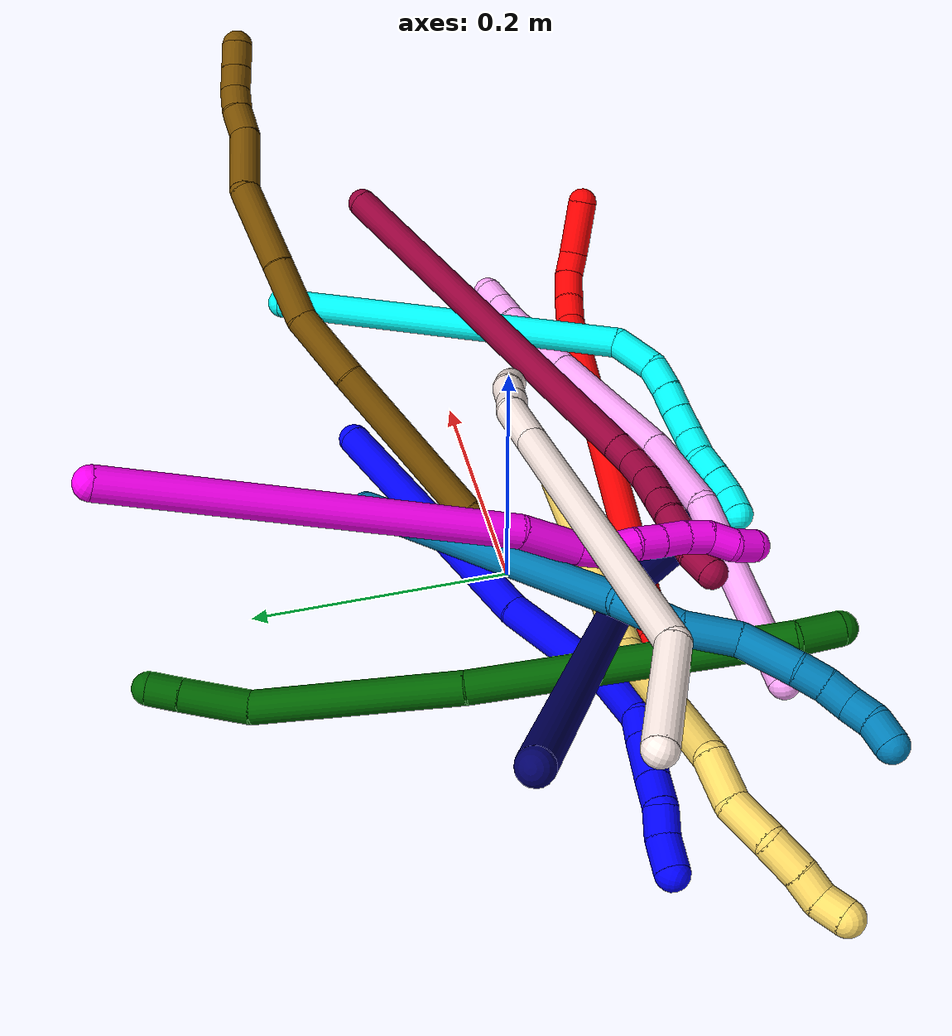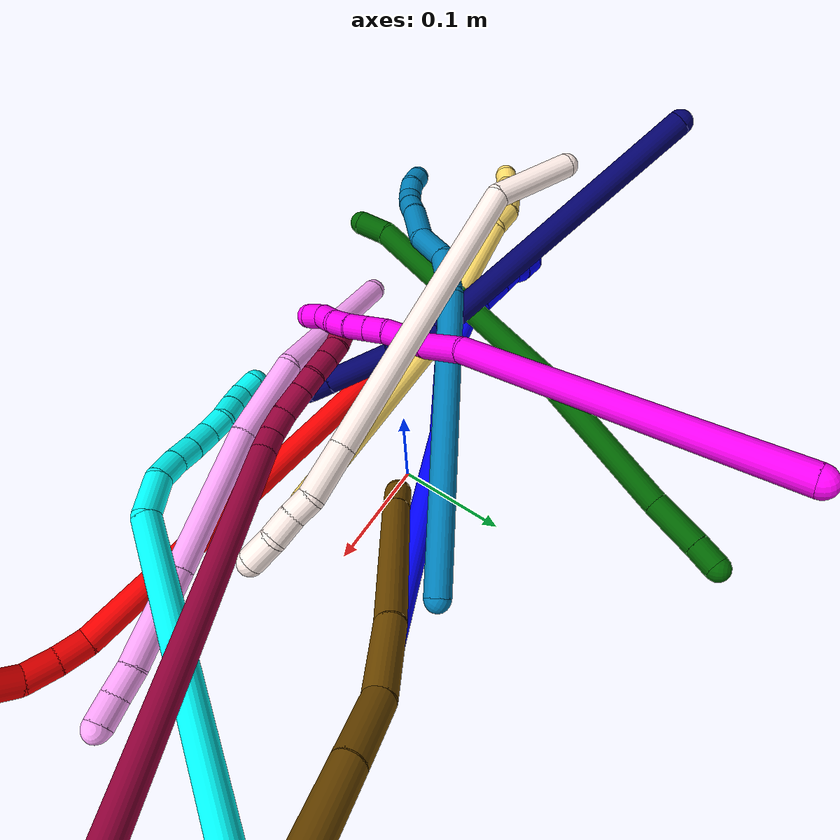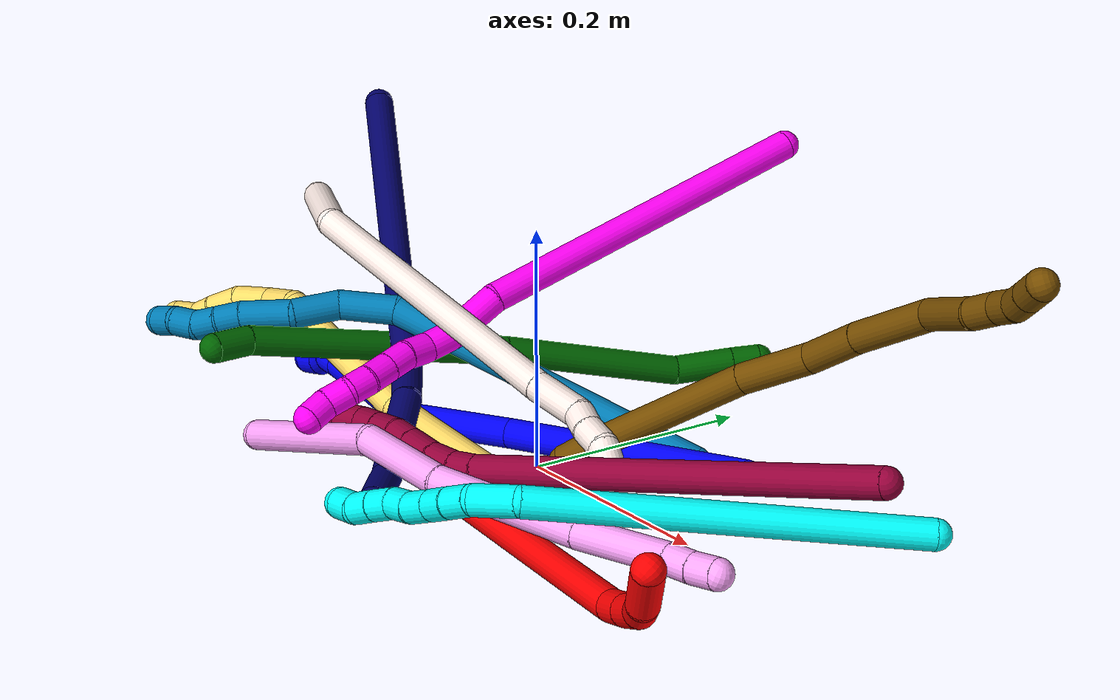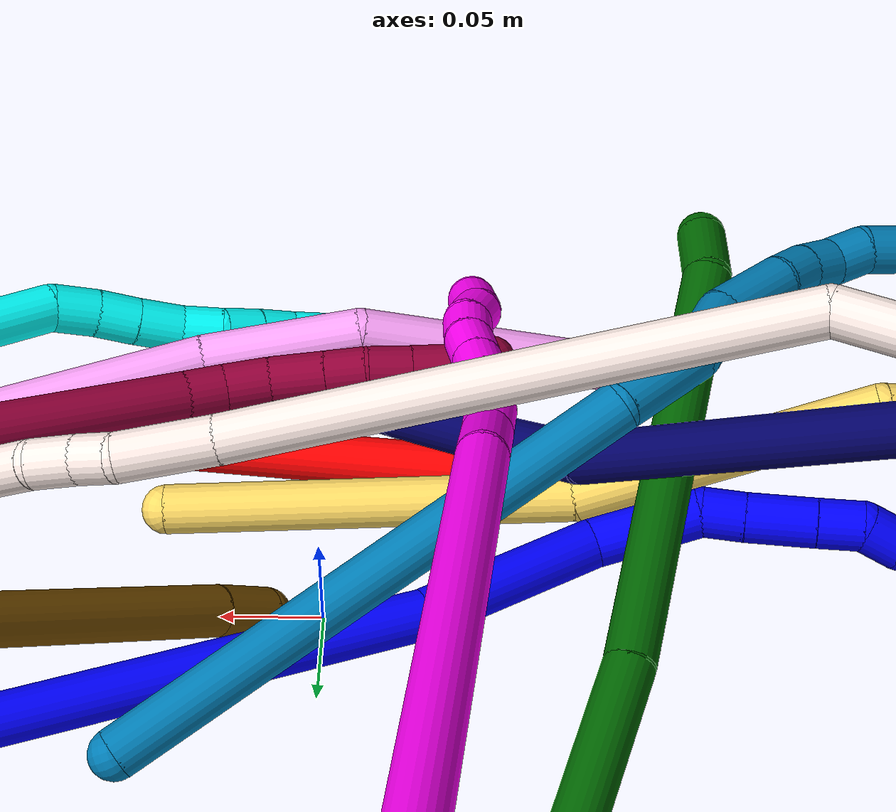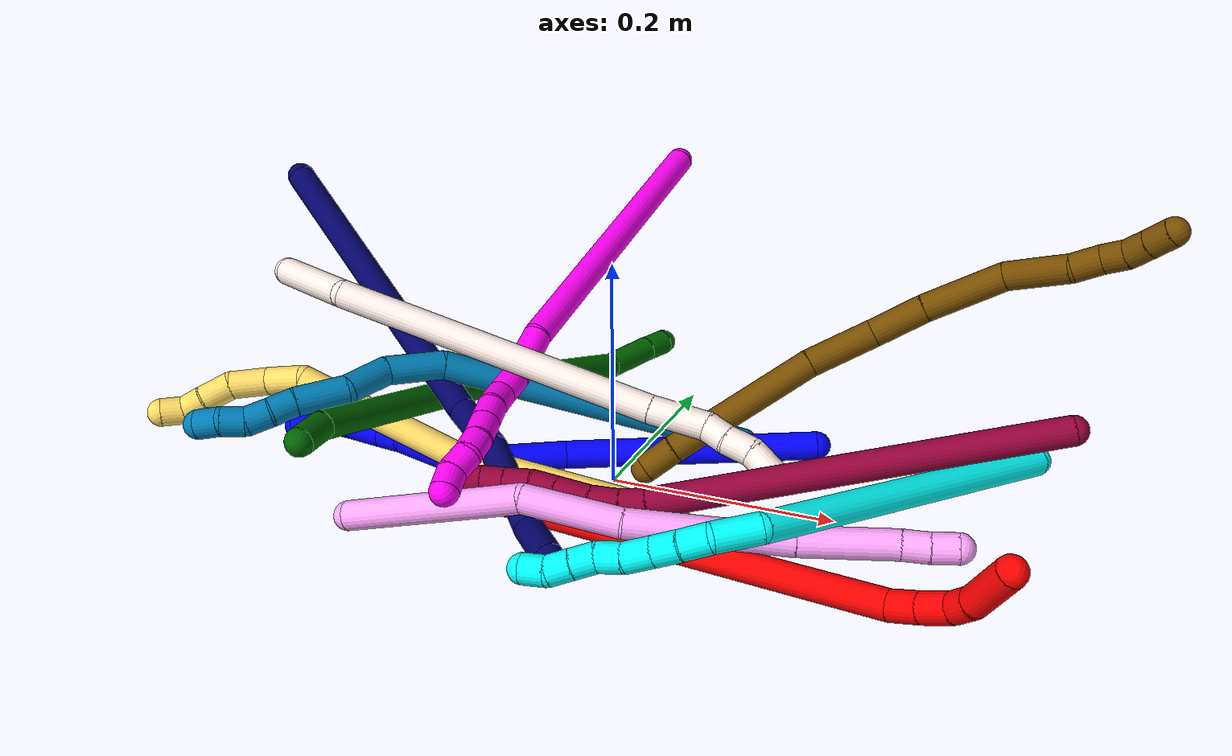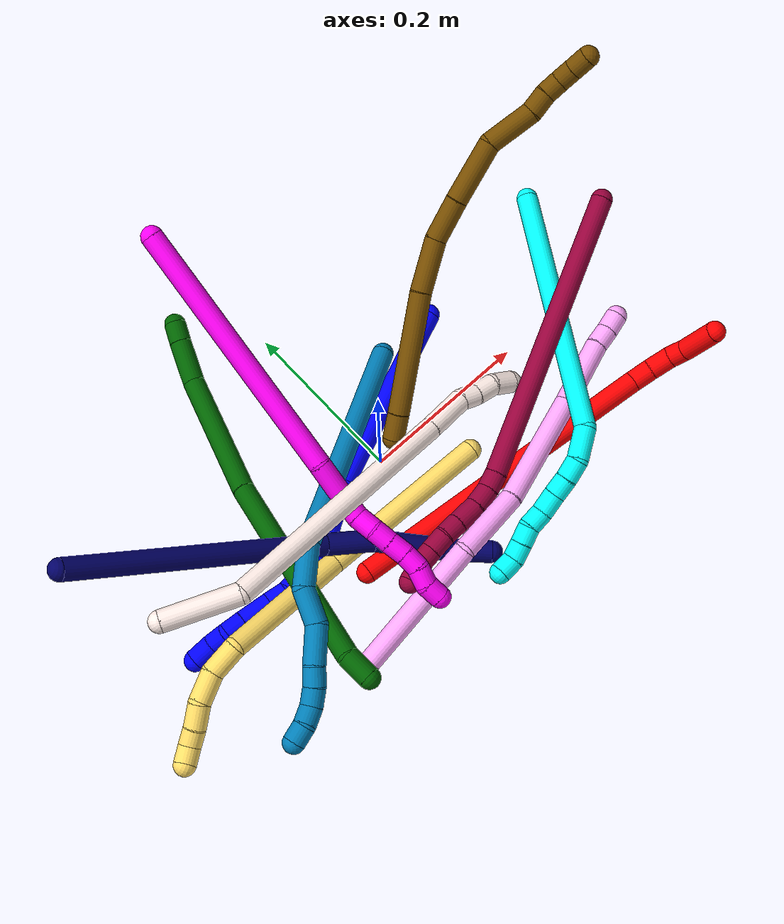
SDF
<sdf version="1.7">
 <world name="default">
  <plugin name="TubeGeneratorPlugin" filename="libtube_generator_plugin.so"/>
  <model name="photoneo_s_sensor">
   <static>1</static>
   <pose>0 0 2 1.57079 1.57079 3.14159</pose>
   <link name="link">
    <inertial><mass>0.1</mass></inertial>
    <sensor name="sensor" type="depth">
     <update_rate>30</update_rate>
     <camera>
      <horizontal_fov>1.22</horizontal_fov>
      <image><width>1920</width><height>1200</height><format>B8G8R8</format></image>
      <clip><near>0.1</near><far>4</far></clip>
      <depth_camera><output>points</output></depth_camera>
     </camera>
     <plugin name="camera_plugin" filename="libgazebo_ros_depth_camera.so">
      <baseline>0.2</baseline>
      <alwaysOn>1</alwaysOn>
      <updateRate>0.0</updateRate>
      <cameraName>camera_ir</cameraName>
      <imageTopicName>/camera/color/image_raw</imageTopicName>
      <cameraInfoTopicName>/camera/color/camera_info</cameraInfoTopicName>
      <depthImageTopicName>/camera/depth/image_raw</depthImageTopicName>
      <depthImageCameraInfoTopicName>/camera/depth/camera_info</depthImageCameraInfoTopicName>
      <pointCloudTopicName>/camera/depth/points</pointCloudTopicName>
      <frameName>fr_optical</frameName>
      <pointCloudCutoff>0.1</pointCloudCutoff>
      <pointCloudCutoffMax>2.0</pointCloudCutoffMax>
      <distortionK1>0</distortionK1>
      <distortionK2>0</distortionK2>
      <distortionK3>0</distortionK3>
      <distortionT1>0</distortionT1>
      <distortionT2>0</distortionT2>
      <CxPrime>0</CxPrime>
      <Cx>0</Cx>
      <Cy>0</Cy>
      <focalLength>0</focalLength>
      <hackBaseline>0</hackBaseline>
     </plugin>
    </sensor>
   </link>
  </model>
  <gravity>0 0 -9.8</gravity>
  <magnetic_field>6e-06 2.3e-05 -4.2e-05</magnetic_field>
  <atmosphere type="adiabatic"/>
  <physics name="default_physics" default="0" type="ode">
   <max_step_size>0.003</max_step_size>
   <real_time_factor>1</real_time_factor>
   <real_time_update_rate>1000</real_time_update_rate>
   <max_contacts>10000</max_contacts>
   <ode>
    <solver>
     <type>quick</type>
     <iters>100</iters>
     <sor>1.3</sor>
     <use_dynamic_moi_rescaling>0</use_dynamic_moi_rescaling>
    </solver>
    <constraints>
     <contact_max_correcting_vel>0</contact_max_correcting_vel>
     <contact_surface_layer>0.001</contact_surface_layer>
     <cfm>0</cfm>
     <erp>0.2</erp>
    </constraints>
   </ode>
  </physics>
  <scene><ambient>0.4 0.4 0.4 1</ambient><background>0.7 0.7 0.7 1</background><shadows>0</shadows></scene>
  <audio><device>default</device></audio>
  <spherical_coordinates>
   <surface_model>EARTH_WGS84</surface_model>
   <latitude_deg>0</latitude_deg>
   <longitude_deg>0</longitude_deg>
   <elevation>0</elevation>
   <heading_deg>0</heading_deg>
  </spherical_coordinates>
  <model name="bin">
   <static>1</static>
   <link name="bottom">
    <collision name="collision-bottom">
     <pose>0 0 -0.01 0 -0 0</pose>
     <geometry><box><size>0.8 0.6 0.02</size></box></geometry>
     <surface>
      <friction><ode><mu>100</mu><mu2>100</mu2></ode></friction>
      <contact><collide_bitmask>65535</collide_bitmask></contact>
     </surface>
    </collision>
   </link>
   <link name="west_wall">
    <collision name="collision-west_wall">
     <pose>-0.41 0 0.1 0 -0 0</pose>
     <geometry><box><size>0.02 0.6 0.2</size></box></geometry>
     <surface>
      <friction><ode><mu>100</mu><mu2>100</mu2></ode></friction>
      <contact><collide_bitmask>65535</collide_bitmask></contact>
     </surface>
    </collision>
   </link>
   <link name="east_wall">
    <collision name="collision-east_wall">
     <pose>0.41 0 0.1 0 -0 0</pose>
     <geometry><box><size>0.02 0.6 0.2</size></box></geometry>
     <surface>
      <friction><ode><mu>100</mu><mu2>100</mu2></ode></friction>
      <contact><collide_bitmask>65535</collide_bitmask></contact>
     </surface>
    </collision>
   </link>
   <link name="south_wall">
    <collision name="collision-south_wall">
     <pose>0 -0.31 0.1 0 -0 0</pose>
     <geometry><box><size>0.8 0.02 0.2</size></box></geometry>
     <surface>
      <friction><ode><mu>100</mu><mu2>100</mu2></ode></friction>
      <contact><collide_bitmask>65535</collide_bitmask></contact>
     </surface>
    </collision>
   </link>
   <link name="north_wall">
    <collision name="collision-north_wall">
     <pose>0 0.31 0.1 0 -0 0</pose>
     <geometry><box><size>0.8 0.02 0.2</size></box></geometry>
     <surface>
      <friction><ode><mu>100</mu><mu2>100</mu2></ode></friction>
      <contact><collide_bitmask>65535</collide_bitmask></contact>
     </surface>
    </collision>
   </link>
  </model>
  <model name="1">
   <static>0</static>
   <link name="1">
    <collision name="collision-cylinder-e_1_1_4">
     <pose>-0.03766 -0.010787 0.104622 0.102737 -0.343837 -0.017854</pose>
     <geometry><cylinder><radius>0.0125</radius><length>0.223432</length></cylinder></geometry>
     <surface>
      <friction><ode><mu>1.16</mu><mu2>1.16</mu2><slip1>0</slip1><slip2>0</slip2></ode></friction>
      <contact><ode><kp>1e+06</kp><kd>1</kd><max_vel>0</max_vel><min_depth>0.001</min_depth></ode></contact>
     </surface>
    </collision>
    <visual name="visual-cylinder-e_1_1_4">
     <pose>-0.03766 -0.010787 0.104622 0.102737 -0.343837 -0.017854</pose>
     <geometry><cylinder><radius>0.0125</radius><length>0.223432</length></cylinder></geometry>
     <material><ambient>0 0 1 1</ambient></material>
    </visual>
    <collision name="collision-cylinder-e_2_4_5">
     <pose>-0.084102 -0.024829 0.256163 0.069285 -0.184614 -0.006416</pose>
     <geometry><cylinder><radius>0.0125</radius><length>0.095689</length></cylinder></geometry>
     <surface>
      <friction><ode><mu>1.16</mu><mu2>1.16</mu2><slip1>0</slip1><slip2>0</slip2></ode></friction>
      <contact><ode><kp>1e+06</kp><kd>1</kd><max_vel>0</max_vel><min_depth>0.001</min_depth></ode></contact>
     </surface>
    </collision>
    <visual name="visual-cylinder-e_2_4_5">
     <pose>-0.084102 -0.024829 0.256163 0.069285 -0.184614 -0.006416</pose>
     <geometry><cylinder><radius>0.0125</radius><length>0.095689</length></cylinder></geometry>
     <material><ambient>0 0 1 1</ambient></material>
    </visual>
    <collision name="collision-cylinder-e_3_5_6">
     <pose>-0.106857 -0.020778 0.325967 -0.309052 -0.526792 0.08396</pose>
     <geometry><cylinder><radius>0.0125</radius><length>0.055582</length></cylinder></geometry>
     <surface>
      <friction><ode><mu>1.16</mu><mu2>1.16</mu2><slip1>0</slip1><slip2>0</slip2></ode></friction>
      <contact><ode><kp>1e+06</kp><kd>1</kd><max_vel>0</max_vel><min_depth>0.001</min_depth></ode></contact>
     </surface>
    </collision>
    <visual name="visual-cylinder-e_3_5_6">
     <pose>-0.106857 -0.020778 0.325967 -0.309052 -0.526792 0.08396</pose>
     <geometry><cylinder><radius>0.0125</radius><length>0.055582</length></cylinder></geometry>
     <material><ambient>0 0 1 1</ambient></material>
    </visual>
    <collision name="collision-cylinder-e_4_6_7">
     <pose>-0.129013 -0.013522 0.355899 0.007242 -0.859899 -0.003321</pose>
     <geometry><cylinder><radius>0.0125</radius><length>0.021598</length></cylinder></geometry>
     <surface>
      <friction><ode><mu>1.16</mu><mu2>1.16</mu2><slip1>0</slip1><slip2>0</slip2></ode></friction>
      <contact><ode><kp>1e+06</kp><kd>1</kd><max_vel>0</max_vel><min_depth>0.001</min_depth></ode></contact>
     </surface>
    </collision>
    <visual name="visual-cylinder-e_4_6_7">
     <pose>-0.129013 -0.013522 0.355899 0.007242 -0.859899 -0.003321</pose>
     <geometry><cylinder><radius>0.0125</radius><length>0.021598</length></cylinder></geometry>
     <material><ambient>0 0 1 1</ambient></material>
    </visual>
    <collision name="collision-cylinder-e_5_7_8">
     <pose>-0.15005 -0.013111 0.374789 -0.039059 -0.825895 0.017115</pose>
     <geometry><cylinder><radius>0.0125</radius><length>0.034969</length></cylinder></geometry>
     <surface>
      <friction><ode><mu>1.16</mu><mu2>1.16</mu2><slip1>0</slip1><slip2>0</slip2></ode></friction>
      <contact><ode><kp>1e+06</kp><kd>1</kd><max_vel>0</max_vel><min_depth>0.001</min_depth></ode></contact>
     </surface>
    </collision>
    <visual name="visual-cylinder-e_5_7_8">
     <pose>-0.15005 -0.013111 0.374789 -0.039059 -0.825895 0.017115</pose>
     <geometry><cylinder><radius>0.0125</radius><length>0.034969</length></cylinder></geometry>
     <material><ambient>0 0 1 1</ambient></material>
    </visual>
    <collision name="collision-cylinder-e_6_8_9">
     <pose>-0.171082 -0.01248 0.394572 -0.02117 -0.800171 0.008953</pose>
     <geometry><cylinder><radius>0.0125</radius><length>0.022799</length></cylinder></geometry>
     <surface>
      <friction><ode><mu>1.16</mu><mu2>1.16</mu2><slip1>0</slip1><slip2>0</slip2></ode></friction>
      <contact><ode><kp>1e+06</kp><kd>1</kd><max_vel>0</max_vel><min_depth>0.001</min_depth></ode></contact>
     </surface>
    </collision>
    <visual name="visual-cylinder-e_6_8_9">
     <pose>-0.171082 -0.01248 0.394572 -0.02117 -0.800171 0.008953</pose>
     <geometry><cylinder><radius>0.0125</radius><length>0.022799</length></cylinder></geometry>
     <material><ambient>0 0 1 1</ambient></material>
    </visual>
    <collision name="collision-cylinder-e_7_9_10">
     <pose>-0.186984 -0.016809 0.407802 0.704494 -0.838399 -0.324711</pose>
     <geometry><cylinder><radius>0.0125</radius><length>0.020771</length></cylinder></geometry>
     <surface>
      <friction><ode><mu>1.16</mu><mu2>1.16</mu2><slip1>0</slip1><slip2>0</slip2></ode></friction>
      <contact><ode><kp>1e+06</kp><kd>1</kd><max_vel>0</max_vel><min_depth>0.001</min_depth></ode></contact>
     </surface>
    </collision>
    <visual name="visual-cylinder-e_7_9_10">
     <pose>-0.186984 -0.016809 0.407802 0.704494 -0.838399 -0.324711</pose>
     <geometry><cylinder><radius>0.0125</radius><length>0.020771</length></cylinder></geometry>
     <material><ambient>0 0 1 1</ambient></material>
    </visual>
    <collision name="collision-cylinder-e_8_10_2">
     <pose>-0.203308 -0.023976 0.421876 0.295028 -0.752873 -0.117339</pose>
     <geometry><cylinder><radius>0.0125</radius><length>0.025159</length></cylinder></geometry>
     <surface>
      <friction><ode><mu>1.16</mu><mu2>1.16</mu2><slip1>0</slip1><slip2>0</slip2></ode></friction>
      <contact><ode><kp>1e+06</kp><kd>1</kd><max_vel>0</max_vel><min_depth>0.001</min_depth></ode></contact>
     </surface>
    </collision>
    <visual name="visual-cylinder-e_8_10_2">
     <pose>-0.203308 -0.023976 0.421876 0.295028 -0.752873 -0.117339</pose>
     <geometry><cylinder><radius>0.0125</radius><length>0.025159</length></cylinder></geometry>
     <material><ambient>0 0 1 1</ambient></material>
    </visual>
    <collision name="collision-sphere-2">
     <pose>-0.211909 -0.026645 0.430659 0 -0 0</pose>
     <geometry><sphere><radius>0.0125</radius></sphere></geometry>
     <surface>
      <friction><ode><mu>1.16</mu><mu2>1.16</mu2><slip1>0</slip1><slip2>0</slip2></ode></friction>
      <contact><ode><kp>1e+06</kp><kd>1</kd><max_vel>0</max_vel><min_depth>0.001</min_depth></ode></contact>
     </surface>
    </collision>
    <visual name="visual-sphere-2">
     <pose>-0.211909 -0.026645 0.430659 0 -0 0</pose>
     <geometry><sphere><radius>0.0125</radius></sphere></geometry>
     <material><ambient>0 0 1 1</ambient></material>
    </visual>
    <collision name="collision-sphere-10">
     <pose>-0.194706 -0.021307 0.413093 0 -0 0</pose>
     <geometry><sphere><radius>0.0125</radius></sphere></geometry>
     <surface>
      <friction><ode><mu>1.16</mu><mu2>1.16</mu2><slip1>0</slip1><slip2>0</slip2></ode></friction>
      <contact><ode><kp>1e+06</kp><kd>1</kd><max_vel>0</max_vel><min_depth>0.001</min_depth></ode></contact>
     </surface>
    </collision>
    <visual name="visual-sphere-10">
     <pose>-0.194706 -0.021307 0.413093 0 -0 0</pose>
     <geometry><sphere><radius>0.0125</radius></sphere></geometry>
     <material><ambient>0 0 1 1</ambient></material>
    </visual>
    <collision name="collision-sphere-9">
     <pose>-0.179261 -0.012312 0.402511 0 -0 0</pose>
     <geometry><sphere><radius>0.0125</radius></sphere></geometry>
     <surface>
      <friction><ode><mu>1.16</mu><mu2>1.16</mu2><slip1>0</slip1><slip2>0</slip2></ode></friction>
      <contact><ode><kp>1e+06</kp><kd>1</kd><max_vel>0</max_vel><min_depth>0.001</min_depth></ode></contact>
     </surface>
    </collision>
    <visual name="visual-sphere-9">
     <pose>-0.179261 -0.012312 0.402511 0 -0 0</pose>
     <geometry><sphere><radius>0.0125</radius></sphere></geometry>
     <material><ambient>0 0 1 1</ambient></material>
    </visual>
    <collision name="collision-sphere-4">
     <pose>-0.075319 -0.021573 0.209245 0 -0 0</pose>
     <geometry><sphere><radius>0.0125</radius></sphere></geometry>
     <surface>
      <friction><ode><mu>1.16</mu><mu2>1.16</mu2><slip1>0</slip1><slip2>0</slip2></ode></friction>
      <contact><ode><kp>1e+06</kp><kd>1</kd><max_vel>0</max_vel><min_depth>0.001</min_depth></ode></contact>
     </surface>
    </collision>
    <visual name="visual-sphere-4">
     <pose>-0.075319 -0.021573 0.209245 0 -0 0</pose>
     <geometry><sphere><radius>0.0125</radius></sphere></geometry>
     <material><ambient>0 0 1 1</ambient></material>
    </visual>
    <collision name="collision-sphere-1">
     <geometry><sphere><radius>0.0125</radius></sphere></geometry>
     <surface>
      <friction><ode><mu>1.16</mu><mu2>1.16</mu2><slip1>0</slip1><slip2>0</slip2></ode></friction>
      <contact><ode><kp>1e+06</kp><kd>1</kd><max_vel>0</max_vel><min_depth>0.001</min_depth></ode></contact>
     </surface>
    </collision>
    <visual name="visual-sphere-1">
     <geometry><sphere><radius>0.0125</radius></sphere></geometry>
     <material><ambient>0 0 1 1</ambient></material>
    </visual>
    <collision name="collision-sphere-8">
     <pose>-0.162903 -0.012648 0.386632 0 -0 0</pose>
     <geometry><sphere><radius>0.0125</radius></sphere></geometry>
     <surface>
      <friction><ode><mu>1.16</mu><mu2>1.16</mu2><slip1>0</slip1><slip2>0</slip2></ode></friction>
      <contact><ode><kp>1e+06</kp><kd>1</kd><max_vel>0</max_vel><min_depth>0.001</min_depth></ode></contact>
     </surface>
    </collision>
    <visual name="visual-sphere-8">
     <pose>-0.162903 -0.012648 0.386632 0 -0 0</pose>
     <geometry><sphere><radius>0.0125</radius></sphere></geometry>
     <material><ambient>0 0 1 1</ambient></material>
    </visual>
    <collision name="collision-sphere-5">
     <pose>-0.092885 -0.028085 0.303082 0 -0 0</pose>
     <geometry><sphere><radius>0.0125</radius></sphere></geometry>
     <surface>
      <friction><ode><mu>1.16</mu><mu2>1.16</mu2><slip1>0</slip1><slip2>0</slip2></ode></friction>
      <contact><ode><kp>1e+06</kp><kd>1</kd><max_vel>0</max_vel><min_depth>0.001</min_depth></ode></contact>
     </surface>
    </collision>
    <visual name="visual-sphere-5">
     <pose>-0.092885 -0.028085 0.303082 0 -0 0</pose>
     <geometry><sphere><radius>0.0125</radius></sphere></geometry>
     <material><ambient>0 0 1 1</ambient></material>
    </visual>
    <collision name="collision-sphere-6">
     <pose>-0.120829 -0.013471 0.348852 0 -0 0</pose>
     <geometry><sphere><radius>0.0125</radius></sphere></geometry>
     <surface>
      <friction><ode><mu>1.16</mu><mu2>1.16</mu2><slip1>0</slip1><slip2>0</slip2></ode></friction>
      <contact><ode><kp>1e+06</kp><kd>1</kd><max_vel>0</max_vel><min_depth>0.001</min_depth></ode></contact>
     </surface>
    </collision>
    <visual name="visual-sphere-6">
     <pose>-0.120829 -0.013471 0.348852 0 -0 0</pose>
     <geometry><sphere><radius>0.0125</radius></sphere></geometry>
     <material><ambient>0 0 1 1</ambient></material>
    </visual>
    <collision name="collision-sphere-7">
     <pose>-0.137196 -0.013574 0.362945 0 -0 0</pose>
     <geometry><sphere><radius>0.0125</radius></sphere></geometry>
     <surface>
      <friction><ode><mu>1.16</mu><mu2>1.16</mu2><slip1>0</slip1><slip2>0</slip2></ode></friction>
      <contact><ode><kp>1e+06</kp><kd>1</kd><max_vel>0</max_vel><min_depth>0.001</min_depth></ode></contact>
     </surface>
    </collision>
    <visual name="visual-sphere-7">
     <pose>-0.137196 -0.013574 0.362945 0 -0 0</pose>
     <geometry><sphere><radius>0.0125</radius></sphere></geometry>
     <material><ambient>0 0 1 1</ambient></material>
    </visual>
    <inertial>
     <pose>-0.086669 -0.015856 0.229759 0 -0 0</pose>
     <mass>0.5</mass>
     <inertia>
      <ixx>0.000949</ixx>
      <ixy>0</ixy>
      <ixz>0</ixz>
      <iyy>0.001021</iyy>
      <iyz>0</iyz>
      <izz>0.000474</izz>
     </inertia>
    </inertial>
   </link>
   <pose>0.157966 0.089884 0.022981 1.48915 -0.088796 -0.851426</pose>
  </model>
  <model name="2">
   <static>0</static>
   <link name="2">
    <collision name="collision-cylinder-e_1_1_4">
     <pose>0.188315 -0.006573 0.024079 0.266497 1.43902 0.233825</pose>
     <geometry><cylinder><radius>0.0125</radius><length>0.379923</length></cylinder></geometry>
     <surface>
      <friction><ode><mu>1.16</mu><mu2>1.16</mu2><slip1>0</slip1><slip2>0</slip2></ode></friction>
      <contact><ode><kp>1e+06</kp><kd>1</kd><max_vel>0</max_vel><min_depth>0.001</min_depth></ode></contact>
     </surface>
    </collision>
    <visual name="visual-cylinder-e_1_1_4">
     <pose>0.188315 -0.006573 0.024079 0.266497 1.43902 0.233825</pose>
     <geometry><cylinder><radius>0.0125</radius><length>0.379923</length></cylinder></geometry>
     <material><ambient>1 0 0 1</ambient></material>
    </visual>
    <collision name="collision-cylinder-e_2_4_5">
     <pose>0.388958 -0.010228 0.048874 -1.33031 1.33172 -1.10446</pose>
     <geometry><cylinder><radius>0.0125</radius><length>0.025379</length></cylinder></geometry>
     <surface>
      <friction><ode><mu>1.16</mu><mu2>1.16</mu2><slip1>0</slip1><slip2>0</slip2></ode></friction>
      <contact><ode><kp>1e+06</kp><kd>1</kd><max_vel>0</max_vel><min_depth>0.001</min_depth></ode></contact>
     </surface>
    </collision>
    <visual name="visual-cylinder-e_2_4_5">
     <pose>0.388958 -0.010228 0.048874 -1.33031 1.33172 -1.10446</pose>
     <geometry><cylinder><radius>0.0125</radius><length>0.025379</length></cylinder></geometry>
     <material><ambient>1 0 0 1</ambient></material>
    </visual>
    <collision name="collision-cylinder-e_3_5_6">
     <pose>0.413849 -0.002646 0.050125 -1.45635 1.21315 -1.10804</pose>
     <geometry><cylinder><radius>0.0125</radius><length>0.026821</length></cylinder></geometry>
     <surface>
      <friction><ode><mu>1.16</mu><mu2>1.16</mu2><slip1>0</slip1><slip2>0</slip2></ode></friction>
      <contact><ode><kp>1e+06</kp><kd>1</kd><max_vel>0</max_vel><min_depth>0.001</min_depth></ode></contact>
     </surface>
    </collision>
    <visual name="visual-cylinder-e_3_5_6">
     <pose>0.413849 -0.002646 0.050125 -1.45635 1.21315 -1.10804</pose>
     <geometry><cylinder><radius>0.0125</radius><length>0.026821</length></cylinder></geometry>
     <material><ambient>1 0 0 1</ambient></material>
    </visual>
    <collision name="collision-cylinder-e_4_6_7">
     <pose>0.43408 0.008692 0.050838 -1.54432 0.854495 -0.834701</pose>
     <geometry><cylinder><radius>0.0125</radius><length>0.020337</length></cylinder></geometry>
     <surface>
      <friction><ode><mu>1.16</mu><mu2>1.16</mu2><slip1>0</slip1><slip2>0</slip2></ode></friction>
      <contact><ode><kp>1e+06</kp><kd>1</kd><max_vel>0</max_vel><min_depth>0.001</min_depth></ode></contact>
     </surface>
    </collision>
    <visual name="visual-cylinder-e_4_6_7">
     <pose>0.43408 0.008692 0.050838 -1.54432 0.854495 -0.834701</pose>
     <geometry><cylinder><radius>0.0125</radius><length>0.020337</length></cylinder></geometry>
     <material><ambient>1 0 0 1</ambient></material>
    </visual>
    <collision name="collision-cylinder-e_5_7_2">
     <pose>0.456087 0.033931 0.047168 -1.77514 0.647488 -0.781989</pose>
     <geometry><cylinder><radius>0.0125</radius><length>0.04754</length></cylinder></geometry>
     <surface>
      <friction><ode><mu>1.16</mu><mu2>1.16</mu2><slip1>0</slip1><slip2>0</slip2></ode></friction>
      <contact><ode><kp>1e+06</kp><kd>1</kd><max_vel>0</max_vel><min_depth>0.001</min_depth></ode></contact>
     </surface>
    </collision>
    <visual name="visual-cylinder-e_5_7_2">
     <pose>0.456087 0.033931 0.047168 -1.77514 0.647488 -0.781989</pose>
     <geometry><cylinder><radius>0.0125</radius><length>0.04754</length></cylinder></geometry>
     <material><ambient>1 0 0 1</ambient></material>
    </visual>
    <collision name="collision-sphere-2">
     <pose>0.470425 0.052495 0.04332 0 -0 0</pose>
     <geometry><sphere><radius>0.0125</radius></sphere></geometry>
     <surface>
      <friction><ode><mu>1.16</mu><mu2>1.16</mu2><slip1>0</slip1><slip2>0</slip2></ode></friction>
      <contact><ode><kp>1e+06</kp><kd>1</kd><max_vel>0</max_vel><min_depth>0.001</min_depth></ode></contact>
     </surface>
    </collision>
    <visual name="visual-sphere-2">
     <pose>0.470425 0.052495 0.04332 0 -0 0</pose>
     <geometry><sphere><radius>0.0125</radius></sphere></geometry>
     <material><ambient>1 0 0 1</ambient></material>
    </visual>
    <collision name="collision-sphere-7">
     <pose>0.441749 0.015366 0.051015 0 -0 0</pose>
     <geometry><sphere><radius>0.0125</radius></sphere></geometry>
     <surface>
      <friction><ode><mu>1.16</mu><mu2>1.16</mu2><slip1>0</slip1><slip2>0</slip2></ode></friction>
      <contact><ode><kp>1e+06</kp><kd>1</kd><max_vel>0</max_vel><min_depth>0.001</min_depth></ode></contact>
     </surface>
    </collision>
    <visual name="visual-sphere-7">
     <pose>0.441749 0.015366 0.051015 0 -0 0</pose>
     <geometry><sphere><radius>0.0125</radius></sphere></geometry>
     <material><ambient>1 0 0 1</ambient></material>
    </visual>
    <collision name="collision-sphere-6">
     <pose>0.426411 0.002018 0.050662 0 -0 0</pose>
     <geometry><sphere><radius>0.0125</radius></sphere></geometry>
     <surface>
      <friction><ode><mu>1.16</mu><mu2>1.16</mu2><slip1>0</slip1><slip2>0</slip2></ode></friction>
      <contact><ode><kp>1e+06</kp><kd>1</kd><max_vel>0</max_vel><min_depth>0.001</min_depth></ode></contact>
     </surface>
    </collision>
    <visual name="visual-sphere-6">
     <pose>0.426411 0.002018 0.050662 0 -0 0</pose>
     <geometry><sphere><radius>0.0125</radius></sphere></geometry>
     <material><ambient>1 0 0 1</ambient></material>
    </visual>
    <collision name="collision-sphere-5">
     <pose>0.401287 -0.00731 0.049589 0 -0 0</pose>
     <geometry><sphere><radius>0.0125</radius></sphere></geometry>
     <surface>
      <friction><ode><mu>1.16</mu><mu2>1.16</mu2><slip1>0</slip1><slip2>0</slip2></ode></friction>
      <contact><ode><kp>1e+06</kp><kd>1</kd><max_vel>0</max_vel><min_depth>0.001</min_depth></ode></contact>
     </surface>
    </collision>
    <visual name="visual-sphere-5">
     <pose>0.401287 -0.00731 0.049589 0 -0 0</pose>
     <geometry><sphere><radius>0.0125</radius></sphere></geometry>
     <material><ambient>1 0 0 1</ambient></material>
    </visual>
    <collision name="collision-sphere-1">
     <geometry><sphere><radius>0.0125</radius></sphere></geometry>
     <surface>
      <friction><ode><mu>1.16</mu><mu2>1.16</mu2><slip1>0</slip1><slip2>0</slip2></ode></friction>
      <contact><ode><kp>1e+06</kp><kd>1</kd><max_vel>0</max_vel><min_depth>0.001</min_depth></ode></contact>
     </surface>
    </collision>
    <visual name="visual-sphere-1">
     <geometry><sphere><radius>0.0125</radius></sphere></geometry>
     <material><ambient>1 0 0 1</ambient></material>
    </visual>
    <collision name="collision-sphere-4">
     <pose>0.37663 -0.013147 0.048158 0 -0 0</pose>
     <geometry><sphere><radius>0.0125</radius></sphere></geometry>
     <surface>
      <friction><ode><mu>1.16</mu><mu2>1.16</mu2><slip1>0</slip1><slip2>0</slip2></ode></friction>
      <contact><ode><kp>1e+06</kp><kd>1</kd><max_vel>0</max_vel><min_depth>0.001</min_depth></ode></contact>
     </surface>
    </collision>
    <visual name="visual-sphere-4">
     <pose>0.37663 -0.013147 0.048158 0 -0 0</pose>
     <geometry><sphere><radius>0.0125</radius></sphere></geometry>
     <material><ambient>1 0 0 1</ambient></material>
    </visual>
    <inertial>
     <pose>0.246053 -0.002076 0.030018 0 -0 0</pose>
     <mass>0.5</mass>
     <inertia>
      <ixx>0.000762</ixx>
      <ixy>0</ixy>
      <ixz>0</ixz>
      <iyy>0.004724</iyy>
      <iyz>0</iyz>
      <izz>-0.004406</izz>
     </inertia>
    </inertial>
   </link>
   <pose>-0.1007 -0.088553 0.011497 2.15232 -0.099073 -0.016593</pose>
  </model>
  <model name="3">
   <static>0</static>
   <link name="3">
    <collision name="collision-cylinder-e_1_1_4">
     <pose>-0.094657 -0.115623 -0.038497 1.8922 -0.660398 -0.887492</pose>
     <geometry><cylinder><radius>0.0125</radius><length>0.308615</length></cylinder></geometry>
     <surface>
      <friction><ode><mu>1.16</mu><mu2>1.16</mu2><slip1>0</slip1><slip2>0</slip2></ode></friction>
      <contact><ode><kp>1e+06</kp><kd>1</kd><max_vel>0</max_vel><min_depth>0.001</min_depth></ode></contact>
     </surface>
    </collision>
    <visual name="visual-cylinder-e_1_1_4">
     <pose>-0.094657 -0.115623 -0.038497 1.8922 -0.660398 -0.887492</pose>
     <geometry><cylinder><radius>0.0125</radius><length>0.308615</length></cylinder></geometry>
     <material><ambient>0.003922 1 0.996078 1</ambient></material>
    </visual>
    <collision name="collision-cylinder-e_2_4_5">
     <pose>-0.200328 -0.240581 -0.089527 2.50141 -0.613937 -1.52607</pose>
     <geometry><cylinder><radius>0.0125</radius><length>0.038236</length></cylinder></geometry>
     <surface>
      <friction><ode><mu>1.16</mu><mu2>1.16</mu2><slip1>0</slip1><slip2>0</slip2></ode></friction>
      <contact><ode><kp>1e+06</kp><kd>1</kd><max_vel>0</max_vel><min_depth>0.001</min_depth></ode></contact>
     </surface>
    </collision>
    <visual name="visual-cylinder-e_2_4_5">
     <pose>-0.200328 -0.240581 -0.089527 2.50141 -0.613937 -1.52607</pose>
     <geometry><cylinder><radius>0.0125</radius><length>0.038236</length></cylinder></geometry>
     <material><ambient>0.003922 1 0.996078 1</ambient></material>
    </visual>
    <collision name="collision-cylinder-e_3_5_6">
     <pose>-0.216016 -0.252771 -0.112659 2.87846 -0.402575 -1.99091</pose>
     <geometry><cylinder><radius>0.0125</radius><length>0.023864</length></cylinder></geometry>
     <surface>
      <friction><ode><mu>1.16</mu><mu2>1.16</mu2><slip1>0</slip1><slip2>0</slip2></ode></friction>
      <contact><ode><kp>1e+06</kp><kd>1</kd><max_vel>0</max_vel><min_depth>0.001</min_depth></ode></contact>
     </surface>
    </collision>
    <visual name="visual-cylinder-e_3_5_6">
     <pose>-0.216016 -0.252771 -0.112659 2.87846 -0.402575 -1.99091</pose>
     <geometry><cylinder><radius>0.0125</radius><length>0.023864</length></cylinder></geometry>
     <material><ambient>0.003922 1 0.996078 1</ambient></material>
    </visual>
    <collision name="collision-cylinder-e_4_6_7">
     <pose>-0.224608 -0.257165 -0.133328 2.99003 -0.367172 -2.36525</pose>
     <geometry><cylinder><radius>0.0125</radius><length>0.021825</length></cylinder></geometry>
     <surface>
      <friction><ode><mu>1.16</mu><mu2>1.16</mu2><slip1>0</slip1><slip2>0</slip2></ode></friction>
      <contact><ode><kp>1e+06</kp><kd>1</kd><max_vel>0</max_vel><min_depth>0.001</min_depth></ode></contact>
     </surface>
    </collision>
    <visual name="visual-cylinder-e_4_6_7">
     <pose>-0.224608 -0.257165 -0.133328 2.99003 -0.367172 -2.36525</pose>
     <geometry><cylinder><radius>0.0125</radius><length>0.021825</length></cylinder></geometry>
     <material><ambient>0.003922 1 0.996078 1</ambient></material>
    </visual>
    <collision name="collision-cylinder-e_5_7_8">
     <pose>-0.233245 -0.260863 -0.154565 2.95052 -0.393285 -2.2449</pose>
     <geometry><cylinder><radius>0.0125</radius><length>0.024634</length></cylinder></geometry>
     <surface>
      <friction><ode><mu>1.16</mu><mu2>1.16</mu2><slip1>0</slip1><slip2>0</slip2></ode></friction>
      <contact><ode><kp>1e+06</kp><kd>1</kd><max_vel>0</max_vel><min_depth>0.001</min_depth></ode></contact>
     </surface>
    </collision>
    <visual name="visual-cylinder-e_5_7_8">
     <pose>-0.233245 -0.260863 -0.154565 2.95052 -0.393285 -2.2449</pose>
     <geometry><cylinder><radius>0.0125</radius><length>0.024634</length></cylinder></geometry>
     <material><ambient>0.003922 1 0.996078 1</ambient></material>
    </visual>
    <collision name="collision-cylinder-e_6_8_9">
     <pose>-0.243979 -0.263433 -0.174745 3.09616 -0.588034 -2.9918</pose>
     <geometry><cylinder><radius>0.0125</radius><length>0.021681</length></cylinder></geometry>
     <surface>
      <friction><ode><mu>1.16</mu><mu2>1.16</mu2><slip1>0</slip1><slip2>0</slip2></ode></friction>
      <contact><ode><kp>1e+06</kp><kd>1</kd><max_vel>0</max_vel><min_depth>0.001</min_depth></ode></contact>
     </surface>
    </collision>
    <visual name="visual-cylinder-e_6_8_9">
     <pose>-0.243979 -0.263433 -0.174745 3.09616 -0.588034 -2.9918</pose>
     <geometry><cylinder><radius>0.0125</radius><length>0.021681</length></cylinder></geometry>
     <material><ambient>0.003922 1 0.996078 1</ambient></material>
    </visual>
    <collision name="collision-cylinder-e_7_9_10">
     <pose>-0.254265 -0.267314 -0.192274 2.75456 -0.434798 -1.69023</pose>
     <geometry><cylinder><radius>0.0125</radius><length>0.020284</length></cylinder></geometry>
     <surface>
      <friction><ode><mu>1.16</mu><mu2>1.16</mu2><slip1>0</slip1><slip2>0</slip2></ode></friction>
      <contact><ode><kp>1e+06</kp><kd>1</kd><max_vel>0</max_vel><min_depth>0.001</min_depth></ode></contact>
     </surface>
    </collision>
    <visual name="visual-cylinder-e_7_9_10">
     <pose>-0.254265 -0.267314 -0.192274 2.75456 -0.434798 -1.69023</pose>
     <geometry><cylinder><radius>0.0125</radius><length>0.020284</length></cylinder></geometry>
     <material><ambient>0.003922 1 0.996078 1</ambient></material>
    </visual>
    <collision name="collision-cylinder-e_8_10_11">
     <pose>-0.262484 -0.273905 -0.209476 2.7968 -0.404207 -1.73282</pose>
     <geometry><cylinder><radius>0.0125</radius><length>0.020073</length></cylinder></geometry>
     <surface>
      <friction><ode><mu>1.16</mu><mu2>1.16</mu2><slip1>0</slip1><slip2>0</slip2></ode></friction>
      <contact><ode><kp>1e+06</kp><kd>1</kd><max_vel>0</max_vel><min_depth>0.001</min_depth></ode></contact>
     </surface>
    </collision>
    <visual name="visual-cylinder-e_8_10_11">
     <pose>-0.262484 -0.273905 -0.209476 2.7968 -0.404207 -1.73282</pose>
     <geometry><cylinder><radius>0.0125</radius><length>0.020073</length></cylinder></geometry>
     <material><ambient>0.003922 1 0.996078 1</ambient></material>
    </visual>
    <collision name="collision-cylinder-e_9_11_2">
     <pose>-0.272549 -0.276958 -0.226564 -3.13369 -0.629278 3.11731</pose>
     <geometry><cylinder><radius>0.0125</radius><length>0.020789</length></cylinder></geometry>
     <surface>
      <friction><ode><mu>1.16</mu><mu2>1.16</mu2><slip1>0</slip1><slip2>0</slip2></ode></friction>
      <contact><ode><kp>1e+06</kp><kd>1</kd><max_vel>0</max_vel><min_depth>0.001</min_depth></ode></contact>
     </surface>
    </collision>
    <visual name="visual-cylinder-e_9_11_2">
     <pose>-0.272549 -0.276958 -0.226564 -3.13369 -0.629278 3.11731</pose>
     <geometry><cylinder><radius>0.0125</radius><length>0.020789</length></cylinder></geometry>
     <material><ambient>0.003922 1 0.996078 1</ambient></material>
    </visual>
    <collision name="collision-sphere-2">
     <pose>-0.278667 -0.276892 -0.234967 0 -0 0</pose>
     <geometry><sphere><radius>0.0125</radius></sphere></geometry>
     <surface>
      <friction><ode><mu>1.16</mu><mu2>1.16</mu2><slip1>0</slip1><slip2>0</slip2></ode></friction>
      <contact><ode><kp>1e+06</kp><kd>1</kd><max_vel>0</max_vel><min_depth>0.001</min_depth></ode></contact>
     </surface>
    </collision>
    <visual name="visual-sphere-2">
     <pose>-0.278667 -0.276892 -0.234967 0 -0 0</pose>
     <geometry><sphere><radius>0.0125</radius></sphere></geometry>
     <material><ambient>0.003922 1 0.996078 1</ambient></material>
    </visual>
    <collision name="collision-sphere-11">
     <pose>-0.266431 -0.277024 -0.218161 0 -0 0</pose>
     <geometry><sphere><radius>0.0125</radius></sphere></geometry>
     <surface>
      <friction><ode><mu>1.16</mu><mu2>1.16</mu2><slip1>0</slip1><slip2>0</slip2></ode></friction>
      <contact><ode><kp>1e+06</kp><kd>1</kd><max_vel>0</max_vel><min_depth>0.001</min_depth></ode></contact>
     </surface>
    </collision>
    <visual name="visual-sphere-11">
     <pose>-0.266431 -0.277024 -0.218161 0 -0 0</pose>
     <geometry><sphere><radius>0.0125</radius></sphere></geometry>
     <material><ambient>0.003922 1 0.996078 1</ambient></material>
    </visual>
    <collision name="collision-sphere-10">
     <pose>-0.258537 -0.270786 -0.200791 0 -0 0</pose>
     <geometry><sphere><radius>0.0125</radius></sphere></geometry>
     <surface>
      <friction><ode><mu>1.16</mu><mu2>1.16</mu2><slip1>0</slip1><slip2>0</slip2></ode></friction>
      <contact><ode><kp>1e+06</kp><kd>1</kd><max_vel>0</max_vel><min_depth>0.001</min_depth></ode></contact>
     </surface>
    </collision>
    <visual name="visual-sphere-10">
     <pose>-0.258537 -0.270786 -0.200791 0 -0 0</pose>
     <geometry><sphere><radius>0.0125</radius></sphere></geometry>
     <material><ambient>0.003922 1 0.996078 1</ambient></material>
    </visual>
    <collision name="collision-sphere-9">
     <pose>-0.249993 -0.263843 -0.183756 0 -0 0</pose>
     <geometry><sphere><radius>0.0125</radius></sphere></geometry>
     <surface>
      <friction><ode><mu>1.16</mu><mu2>1.16</mu2><slip1>0</slip1><slip2>0</slip2></ode></friction>
      <contact><ode><kp>1e+06</kp><kd>1</kd><max_vel>0</max_vel><min_depth>0.001</min_depth></ode></contact>
     </surface>
    </collision>
    <visual name="visual-sphere-9">
     <pose>-0.249993 -0.263843 -0.183756 0 -0 0</pose>
     <geometry><sphere><radius>0.0125</radius></sphere></geometry>
     <material><ambient>0.003922 1 0.996078 1</ambient></material>
    </visual>
    <collision name="collision-sphere-4">
     <pose>-0.189314 -0.231247 -0.076994 0 -0 0</pose>
     <geometry><sphere><radius>0.0125</radius></sphere></geometry>
     <surface>
      <friction><ode><mu>1.16</mu><mu2>1.16</mu2><slip1>0</slip1><slip2>0</slip2></ode></friction>
      <contact><ode><kp>1e+06</kp><kd>1</kd><max_vel>0</max_vel><min_depth>0.001</min_depth></ode></contact>
     </surface>
    </collision>
    <visual name="visual-sphere-4">
     <pose>-0.189314 -0.231247 -0.076994 0 -0 0</pose>
     <geometry><sphere><radius>0.0125</radius></sphere></geometry>
     <material><ambient>0.003922 1 0.996078 1</ambient></material>
    </visual>
    <collision name="collision-sphere-1">
     <geometry><sphere><radius>0.0125</radius></sphere></geometry>
     <surface>
      <friction><ode><mu>1.16</mu><mu2>1.16</mu2><slip1>0</slip1><slip2>0</slip2></ode></friction>
      <contact><ode><kp>1e+06</kp><kd>1</kd><max_vel>0</max_vel><min_depth>0.001</min_depth></ode></contact>
     </surface>
    </collision>
    <visual name="visual-sphere-1">
     <geometry><sphere><radius>0.0125</radius></sphere></geometry>
     <material><ambient>0.003922 1 0.996078 1</ambient></material>
    </visual>
    <collision name="collision-sphere-8">
     <pose>-0.237966 -0.263023 -0.165735 0 -0 0</pose>
     <geometry><sphere><radius>0.0125</radius></sphere></geometry>
     <surface>
      <friction><ode><mu>1.16</mu><mu2>1.16</mu2><slip1>0</slip1><slip2>0</slip2></ode></friction>
      <contact><ode><kp>1e+06</kp><kd>1</kd><max_vel>0</max_vel><min_depth>0.001</min_depth></ode></contact>
     </surface>
    </collision>
    <visual name="visual-sphere-8">
     <pose>-0.237966 -0.263023 -0.165735 0 -0 0</pose>
     <geometry><sphere><radius>0.0125</radius></sphere></geometry>
     <material><ambient>0.003922 1 0.996078 1</ambient></material>
    </visual>
    <collision name="collision-sphere-5">
     <pose>-0.211341 -0.249916 -0.102059 0 -0 0</pose>
     <geometry><sphere><radius>0.0125</radius></sphere></geometry>
     <surface>
      <friction><ode><mu>1.16</mu><mu2>1.16</mu2><slip1>0</slip1><slip2>0</slip2></ode></friction>
      <contact><ode><kp>1e+06</kp><kd>1</kd><max_vel>0</max_vel><min_depth>0.001</min_depth></ode></contact>
     </surface>
    </collision>
    <visual name="visual-sphere-5">
     <pose>-0.211341 -0.249916 -0.102059 0 -0 0</pose>
     <geometry><sphere><radius>0.0125</radius></sphere></geometry>
     <material><ambient>0.003922 1 0.996078 1</ambient></material>
    </visual>
    <collision name="collision-sphere-6">
     <pose>-0.220691 -0.255627 -0.123259 0 -0 0</pose>
     <geometry><sphere><radius>0.0125</radius></sphere></geometry>
     <surface>
      <friction><ode><mu>1.16</mu><mu2>1.16</mu2><slip1>0</slip1><slip2>0</slip2></ode></friction>
      <contact><ode><kp>1e+06</kp><kd>1</kd><max_vel>0</max_vel><min_depth>0.001</min_depth></ode></contact>
     </surface>
    </collision>
    <visual name="visual-sphere-6">
     <pose>-0.220691 -0.255627 -0.123259 0 -0 0</pose>
     <geometry><sphere><radius>0.0125</radius></sphere></geometry>
     <material><ambient>0.003922 1 0.996078 1</ambient></material>
    </visual>
    <collision name="collision-sphere-7">
     <pose>-0.228525 -0.258702 -0.143396 0 -0 0</pose>
     <geometry><sphere><radius>0.0125</radius></sphere></geometry>
     <surface>
      <friction><ode><mu>1.16</mu><mu2>1.16</mu2><slip1>0</slip1><slip2>0</slip2></ode></friction>
      <contact><ode><kp>1e+06</kp><kd>1</kd><max_vel>0</max_vel><min_depth>0.001</min_depth></ode></contact>
     </surface>
    </collision>
    <visual name="visual-sphere-7">
     <pose>-0.228525 -0.258702 -0.143396 0 -0 0</pose>
     <geometry><sphere><radius>0.0125</radius></sphere></geometry>
     <material><ambient>0.003922 1 0.996078 1</ambient></material>
    </visual>
    <inertial>
     <pose>-0.148114 -0.170684 -0.082627 0 -0 0</pose>
     <mass>0.5</mass>
     <inertia>
      <ixx>-0.00032</ixx>
      <ixy>0</ixy>
      <ixz>0</ixz>
      <iyy>-0.000912</iyy>
      <iyz>0</iyz>
      <izz>0.00335</izz>
     </inertia>
    </inertial>
   </link>
   <pose>0.344617 0.118759 0.029815 0.35866 0.814144 0.343144</pose>
  </model>
  <model name="4">
   <static>0</static>
   <link name="4">
    <collision name="collision-cylinder-e_1_1_4">
     <pose>0.063424 0.019611 0.044078 -0.41861 0.920508 -0.209843</pose>
     <geometry><cylinder><radius>0.0125</radius><length>0.159375</length></cylinder></geometry>
     <surface>
      <friction><ode><mu>1.16</mu><mu2>1.16</mu2><slip1>0</slip1><slip2>0</slip2></ode></friction>
      <contact><ode><kp>1e+06</kp><kd>1</kd><max_vel>0</max_vel><min_depth>0.001</min_depth></ode></contact>
     </surface>
    </collision>
    <visual name="visual-cylinder-e_1_1_4">
     <pose>0.063424 0.019611 0.044078 -0.41861 0.920508 -0.209843</pose>
     <geometry><cylinder><radius>0.0125</radius><length>0.159375</length></cylinder></geometry>
     <material><ambient>1 0.65098 0.996078 1</ambient></material>
    </visual>
    <collision name="collision-cylinder-e_2_4_5">
     <pose>0.163756 0.055548 0.097233 -1.06341 1.10227 -0.69386</pose>
     <geometry><cylinder><radius>0.0125</radius><length>0.082732</length></cylinder></geometry>
     <surface>
      <friction><ode><mu>1.16</mu><mu2>1.16</mu2><slip1>0</slip1><slip2>0</slip2></ode></friction>
      <contact><ode><kp>1e+06</kp><kd>1</kd><max_vel>0</max_vel><min_depth>0.001</min_depth></ode></contact>
     </surface>
    </collision>
    <visual name="visual-cylinder-e_2_4_5">
     <pose>0.163756 0.055548 0.097233 -1.06341 1.10227 -0.69386</pose>
     <geometry><cylinder><radius>0.0125</radius><length>0.082732</length></cylinder></geometry>
     <material><ambient>1 0.65098 0.996078 1</ambient></material>
    </visual>
    <collision name="collision-cylinder-e_3_5_6">
     <pose>0.253405 0.108123 0.125556 -1.08269 0.909505 -0.571839</pose>
     <geometry><cylinder><radius>0.0125</radius><length>0.133656</length></cylinder></geometry>
     <surface>
      <friction><ode><mu>1.16</mu><mu2>1.16</mu2><slip1>0</slip1><slip2>0</slip2></ode></friction>
      <contact><ode><kp>1e+06</kp><kd>1</kd><max_vel>0</max_vel><min_depth>0.001</min_depth></ode></contact>
     </surface>
    </collision>
    <visual name="visual-cylinder-e_3_5_6">
     <pose>0.253405 0.108123 0.125556 -1.08269 0.909505 -0.571839</pose>
     <geometry><cylinder><radius>0.0125</radius><length>0.133656</length></cylinder></geometry>
     <material><ambient>1 0.65098 0.996078 1</ambient></material>
    </visual>
    <collision name="collision-cylinder-e_4_6_7">
     <pose>0.336674 0.165978 0.159047 -0.987946 0.867626 -0.488937</pose>
     <geometry><cylinder><radius>0.0125</radius><length>0.080042</length></cylinder></geometry>
     <surface>
      <friction><ode><mu>1.16</mu><mu2>1.16</mu2><slip1>0</slip1><slip2>0</slip2></ode></friction>
      <contact><ode><kp>1e+06</kp><kd>1</kd><max_vel>0</max_vel><min_depth>0.001</min_depth></ode></contact>
     </surface>
    </collision>
    <visual name="visual-cylinder-e_4_6_7">
     <pose>0.336674 0.165978 0.159047 -0.987946 0.867626 -0.488937</pose>
     <geometry><cylinder><radius>0.0125</radius><length>0.080042</length></cylinder></geometry>
     <material><ambient>1 0.65098 0.996078 1</ambient></material>
    </visual>
    <collision name="collision-cylinder-e_5_7_8">
     <pose>0.376629 0.192544 0.176985 -0.930529 0.990211 -0.529425</pose>
     <geometry><cylinder><radius>0.0125</radius><length>0.02255</length></cylinder></geometry>
     <surface>
      <friction><ode><mu>1.16</mu><mu2>1.16</mu2><slip1>0</slip1><slip2>0</slip2></ode></friction>
      <contact><ode><kp>1e+06</kp><kd>1</kd><max_vel>0</max_vel><min_depth>0.001</min_depth></ode></contact>
     </surface>
    </collision>
    <visual name="visual-cylinder-e_5_7_8">
     <pose>0.376629 0.192544 0.176985 -0.930529 0.990211 -0.529425</pose>
     <geometry><cylinder><radius>0.0125</radius><length>0.02255</length></cylinder></geometry>
     <material><ambient>1 0.65098 0.996078 1</ambient></material>
    </visual>
    <collision name="collision-cylinder-e_6_8_2">
     <pose>0.394591 0.202561 0.185007 -0.862999 0.908458 -0.442292</pose>
     <geometry><cylinder><radius>0.0125</radius><length>0.021645</length></cylinder></geometry>
     <surface>
      <friction><ode><mu>1.16</mu><mu2>1.16</mu2><slip1>0</slip1><slip2>0</slip2></ode></friction>
      <contact><ode><kp>1e+06</kp><kd>1</kd><max_vel>0</max_vel><min_depth>0.001</min_depth></ode></contact>
     </surface>
    </collision>
    <visual name="visual-cylinder-e_6_8_2">
     <pose>0.394591 0.202561 0.185007 -0.862999 0.908458 -0.442292</pose>
     <geometry><cylinder><radius>0.0125</radius><length>0.021645</length></cylinder></geometry>
     <material><ambient>1 0.65098 0.996078 1</ambient></material>
    </visual>
    <collision name="collision-sphere-2">
     <pose>0.403125 0.207617 0.189334 0 -0 0</pose>
     <geometry><sphere><radius>0.0125</radius></sphere></geometry>
     <surface>
      <friction><ode><mu>1.16</mu><mu2>1.16</mu2><slip1>0</slip1><slip2>0</slip2></ode></friction>
      <contact><ode><kp>1e+06</kp><kd>1</kd><max_vel>0</max_vel><min_depth>0.001</min_depth></ode></contact>
     </surface>
    </collision>
    <visual name="visual-sphere-2">
     <pose>0.403125 0.207617 0.189334 0 -0 0</pose>
     <geometry><sphere><radius>0.0125</radius></sphere></geometry>
     <material><ambient>1 0.65098 0.996078 1</ambient></material>
    </visual>
    <collision name="collision-sphere-4">
     <pose>0.126848 0.039221 0.088157 0 -0 0</pose>
     <geometry><sphere><radius>0.0125</radius></sphere></geometry>
     <surface>
      <friction><ode><mu>1.16</mu><mu2>1.16</mu2><slip1>0</slip1><slip2>0</slip2></ode></friction>
      <contact><ode><kp>1e+06</kp><kd>1</kd><max_vel>0</max_vel><min_depth>0.001</min_depth></ode></contact>
     </surface>
    </collision>
    <visual name="visual-sphere-4">
     <pose>0.126848 0.039221 0.088157 0 -0 0</pose>
     <geometry><sphere><radius>0.0125</radius></sphere></geometry>
     <material><ambient>1 0.65098 0.996078 1</ambient></material>
    </visual>
    <collision name="collision-sphere-1">
     <geometry><sphere><radius>0.0125</radius></sphere></geometry>
     <surface>
      <friction><ode><mu>1.16</mu><mu2>1.16</mu2><slip1>0</slip1><slip2>0</slip2></ode></friction>
      <contact><ode><kp>1e+06</kp><kd>1</kd><max_vel>0</max_vel><min_depth>0.001</min_depth></ode></contact>
     </surface>
    </collision>
    <visual name="visual-sphere-1">
     <geometry><sphere><radius>0.0125</radius></sphere></geometry>
     <material><ambient>1 0.65098 0.996078 1</ambient></material>
    </visual>
    <collision name="collision-sphere-8">
     <pose>0.386056 0.197504 0.18068 0 -0 0</pose>
     <geometry><sphere><radius>0.0125</radius></sphere></geometry>
     <surface>
      <friction><ode><mu>1.16</mu><mu2>1.16</mu2><slip1>0</slip1><slip2>0</slip2></ode></friction>
      <contact><ode><kp>1e+06</kp><kd>1</kd><max_vel>0</max_vel><min_depth>0.001</min_depth></ode></contact>
     </surface>
    </collision>
    <visual name="visual-sphere-8">
     <pose>0.386056 0.197504 0.18068 0 -0 0</pose>
     <geometry><sphere><radius>0.0125</radius></sphere></geometry>
     <material><ambient>1 0.65098 0.996078 1</ambient></material>
    </visual>
    <collision name="collision-sphere-5">
     <pose>0.200665 0.071874 0.10631 0 -0 0</pose>
     <geometry><sphere><radius>0.0125</radius></sphere></geometry>
     <surface>
      <friction><ode><mu>1.16</mu><mu2>1.16</mu2><slip1>0</slip1><slip2>0</slip2></ode></friction>
      <contact><ode><kp>1e+06</kp><kd>1</kd><max_vel>0</max_vel><min_depth>0.001</min_depth></ode></contact>
     </surface>
    </collision>
    <visual name="visual-sphere-5">
     <pose>0.200665 0.071874 0.10631 0 -0 0</pose>
     <geometry><sphere><radius>0.0125</radius></sphere></geometry>
     <material><ambient>1 0.65098 0.996078 1</ambient></material>
    </visual>
    <collision name="collision-sphere-6">
     <pose>0.306146 0.144372 0.144803 0 -0 0</pose>
     <geometry><sphere><radius>0.0125</radius></sphere></geometry>
     <surface>
      <friction><ode><mu>1.16</mu><mu2>1.16</mu2><slip1>0</slip1><slip2>0</slip2></ode></friction>
      <contact><ode><kp>1e+06</kp><kd>1</kd><max_vel>0</max_vel><min_depth>0.001</min_depth></ode></contact>
     </surface>
    </collision>
    <visual name="visual-sphere-6">
     <pose>0.306146 0.144372 0.144803 0 -0 0</pose>
     <geometry><sphere><radius>0.0125</radius></sphere></geometry>
     <material><ambient>1 0.65098 0.996078 1</ambient></material>
    </visual>
    <collision name="collision-sphere-7">
     <pose>0.367201 0.187585 0.173291 0 -0 0</pose>
     <geometry><sphere><radius>0.0125</radius></sphere></geometry>
     <surface>
      <friction><ode><mu>1.16</mu><mu2>1.16</mu2><slip1>0</slip1><slip2>0</slip2></ode></friction>
      <contact><ode><kp>1e+06</kp><kd>1</kd><max_vel>0</max_vel><min_depth>0.001</min_depth></ode></contact>
     </surface>
    </collision>
    <visual name="visual-sphere-7">
     <pose>0.367201 0.187585 0.173291 0 -0 0</pose>
     <geometry><sphere><radius>0.0125</radius></sphere></geometry>
     <material><ambient>1 0.65098 0.996078 1</ambient></material>
    </visual>
    <inertial>
     <pose>0.203014 0.088368 0.105153 0 -0 0</pose>
     <mass>0.5</mass>
     <inertia>
      <ixx>0.000245</ixx>
      <ixy>0</ixy>
      <ixz>0</ixz>
      <iyy>0.000446</iyy>
      <iyz>0</iyz>
      <izz>-0.000744</izz>
     </inertia>
    </inertial>
   </link>
   <pose>-0.166046 -0.165138 0.01208 -0.294125 0.243834 -0.329767</pose>
  </model>
  <model name="5">
   <static>0</static>
   <link name="5">
    <collision name="collision-cylinder-e_1_1_4">
     <pose>-0.082999 -0.002765 0.060134 0.045954 -0.943303 -0.023442</pose>
     <geometry><cylinder><radius>0.0125</radius><length>0.205063</length></cylinder></geometry>
     <surface>
      <friction><ode><mu>1.16</mu><mu2>1.16</mu2><slip1>0</slip1><slip2>0</slip2></ode></friction>
      <contact><ode><kp>1e+06</kp><kd>1</kd><max_vel>0</max_vel><min_depth>0.001</min_depth></ode></contact>
     </surface>
    </collision>
    <visual name="visual-cylinder-e_1_1_4">
     <pose>-0.082999 -0.002765 0.060134 0.045954 -0.943303 -0.023442</pose>
     <geometry><cylinder><radius>0.0125</radius><length>0.205063</length></cylinder></geometry>
     <material><ambient>1 0.858824 0.4 1</ambient></material>
    </visual>
    <collision name="collision-cylinder-e_2_4_5">
     <pose>-0.221407 -0.027535 0.171129 0.408327 -0.785328 -0.171089</pose>
     <geometry><cylinder><radius>0.0125</radius><length>0.156728</length></cylinder></geometry>
     <surface>
      <friction><ode><mu>1.16</mu><mu2>1.16</mu2><slip1>0</slip1><slip2>0</slip2></ode></friction>
      <contact><ode><kp>1e+06</kp><kd>1</kd><max_vel>0</max_vel><min_depth>0.001</min_depth></ode></contact>
     </surface>
    </collision>
    <visual name="visual-cylinder-e_2_4_5">
     <pose>-0.221407 -0.027535 0.171129 0.408327 -0.785328 -0.171089</pose>
     <geometry><cylinder><radius>0.0125</radius><length>0.156728</length></cylinder></geometry>
     <material><ambient>1 0.858824 0.4 1</ambient></material>
    </visual>
    <collision name="collision-cylinder-e_3_5_6">
     <pose>-0.293358 -0.047727 0.228743 -0.26208 -1.17087 0.174307</pose>
     <geometry><cylinder><radius>0.0125</radius><length>0.035922</length></cylinder></geometry>
     <surface>
      <friction><ode><mu>1.16</mu><mu2>1.16</mu2><slip1>0</slip1><slip2>0</slip2></ode></friction>
      <contact><ode><kp>1e+06</kp><kd>1</kd><max_vel>0</max_vel><min_depth>0.001</min_depth></ode></contact>
     </surface>
    </collision>
    <visual name="visual-cylinder-e_3_5_6">
     <pose>-0.293358 -0.047727 0.228743 -0.26208 -1.17087 0.174307</pose>
     <geometry><cylinder><radius>0.0125</radius><length>0.035922</length></cylinder></geometry>
     <material><ambient>1 0.858824 0.4 1</ambient></material>
    </visual>
    <collision name="collision-cylinder-e_4_6_7">
     <pose>-0.326416 -0.048795 0.238171 0.822444 -1.33714 -0.663491</pose>
     <geometry><cylinder><radius>0.0125</radius><length>0.033951</length></cylinder></geometry>
     <surface>
      <friction><ode><mu>1.16</mu><mu2>1.16</mu2><slip1>0</slip1><slip2>0</slip2></ode></friction>
      <contact><ode><kp>1e+06</kp><kd>1</kd><max_vel>0</max_vel><min_depth>0.001</min_depth></ode></contact>
     </surface>
    </collision>
    <visual name="visual-cylinder-e_4_6_7">
     <pose>-0.326416 -0.048795 0.238171 0.822444 -1.33714 -0.663491</pose>
     <geometry><cylinder><radius>0.0125</radius><length>0.033951</length></cylinder></geometry>
     <material><ambient>1 0.858824 0.4 1</ambient></material>
    </visual>
    <collision name="collision-cylinder-e_5_7_8">
     <pose>-0.356383 -0.051631 0.238719 -3.12077 -1.41394 3.11722</pose>
     <geometry><cylinder><radius>0.0125</radius><length>0.02724</length></cylinder></geometry>
     <surface>
      <friction><ode><mu>1.16</mu><mu2>1.16</mu2><slip1>0</slip1><slip2>0</slip2></ode></friction>
      <contact><ode><kp>1e+06</kp><kd>1</kd><max_vel>0</max_vel><min_depth>0.001</min_depth></ode></contact>
     </surface>
    </collision>
    <visual name="visual-cylinder-e_5_7_8">
     <pose>-0.356383 -0.051631 0.238719 -3.12077 -1.41394 3.11722</pose>
     <geometry><cylinder><radius>0.0125</radius><length>0.02724</length></cylinder></geometry>
     <material><ambient>1 0.858824 0.4 1</ambient></material>
    </visual>
    <collision name="collision-cylinder-e_6_8_9">
     <pose>-0.37991 -0.050213 0.235351 -2.30477 -1.38907 2.16091</pose>
     <geometry><cylinder><radius>0.0125</radius><length>0.020485</length></cylinder></geometry>
     <surface>
      <friction><ode><mu>1.16</mu><mu2>1.16</mu2><slip1>0</slip1><slip2>0</slip2></ode></friction>
      <contact><ode><kp>1e+06</kp><kd>1</kd><max_vel>0</max_vel><min_depth>0.001</min_depth></ode></contact>
     </surface>
    </collision>
    <visual name="visual-cylinder-e_6_8_9">
     <pose>-0.37991 -0.050213 0.235351 -2.30477 -1.38907 2.16091</pose>
     <geometry><cylinder><radius>0.0125</radius><length>0.020485</length></cylinder></geometry>
     <material><ambient>1 0.858824 0.4 1</ambient></material>
    </visual>
    <collision name="collision-cylinder-e_7_9_2">
     <pose>-0.399679 -0.052269 0.234766 1.38237 -1.225 -1.05315</pose>
     <geometry><cylinder><radius>0.0125</radius><length>0.02061</length></cylinder></geometry>
     <surface>
      <friction><ode><mu>1.16</mu><mu2>1.16</mu2><slip1>0</slip1><slip2>0</slip2></ode></friction>
      <contact><ode><kp>1e+06</kp><kd>1</kd><max_vel>0</max_vel><min_depth>0.001</min_depth></ode></contact>
     </surface>
    </collision>
    <visual name="visual-cylinder-e_7_9_2">
     <pose>-0.399679 -0.052269 0.234766 1.38237 -1.225 -1.05315</pose>
     <geometry><cylinder><radius>0.0125</radius><length>0.02061</length></cylinder></geometry>
     <material><ambient>1 0.858824 0.4 1</ambient></material>
    </visual>
    <collision name="collision-sphere-2">
     <pose>-0.409375 -0.0557 0.23542 0 -0 0</pose>
     <geometry><sphere><radius>0.0125</radius></sphere></geometry>
     <surface>
      <friction><ode><mu>1.16</mu><mu2>1.16</mu2><slip1>0</slip1><slip2>0</slip2></ode></friction>
      <contact><ode><kp>1e+06</kp><kd>1</kd><max_vel>0</max_vel><min_depth>0.001</min_depth></ode></contact>
     </surface>
    </collision>
    <visual name="visual-sphere-2">
     <pose>-0.409375 -0.0557 0.23542 0 -0 0</pose>
     <geometry><sphere><radius>0.0125</radius></sphere></geometry>
     <material><ambient>1 0.858824 0.4 1</ambient></material>
    </visual>
    <collision name="collision-sphere-9">
     <pose>-0.389984 -0.048838 0.234111 0 -0 0</pose>
     <geometry><sphere><radius>0.0125</radius></sphere></geometry>
     <surface>
      <friction><ode><mu>1.16</mu><mu2>1.16</mu2><slip1>0</slip1><slip2>0</slip2></ode></friction>
      <contact><ode><kp>1e+06</kp><kd>1</kd><max_vel>0</max_vel><min_depth>0.001</min_depth></ode></contact>
     </surface>
    </collision>
    <visual name="visual-sphere-9">
     <pose>-0.389984 -0.048838 0.234111 0 -0 0</pose>
     <geometry><sphere><radius>0.0125</radius></sphere></geometry>
     <material><ambient>1 0.858824 0.4 1</ambient></material>
    </visual>
    <collision name="collision-sphere-4">
     <pose>-0.165999 -0.005531 0.120269 0 -0 0</pose>
     <geometry><sphere><radius>0.0125</radius></sphere></geometry>
     <surface>
      <friction><ode><mu>1.16</mu><mu2>1.16</mu2><slip1>0</slip1><slip2>0</slip2></ode></friction>
      <contact><ode><kp>1e+06</kp><kd>1</kd><max_vel>0</max_vel><min_depth>0.001</min_depth></ode></contact>
     </surface>
    </collision>
    <visual name="visual-sphere-4">
     <pose>-0.165999 -0.005531 0.120269 0 -0 0</pose>
     <geometry><sphere><radius>0.0125</radius></sphere></geometry>
     <material><ambient>1 0.858824 0.4 1</ambient></material>
    </visual>
    <collision name="collision-sphere-1">
     <geometry><sphere><radius>0.0125</radius></sphere></geometry>
     <surface>
      <friction><ode><mu>1.16</mu><mu2>1.16</mu2><slip1>0</slip1><slip2>0</slip2></ode></friction>
      <contact><ode><kp>1e+06</kp><kd>1</kd><max_vel>0</max_vel><min_depth>0.001</min_depth></ode></contact>
     </surface>
    </collision>
    <visual name="visual-sphere-1">
     <geometry><sphere><radius>0.0125</radius></sphere></geometry>
     <material><ambient>1 0.858824 0.4 1</ambient></material>
    </visual>
    <collision name="collision-sphere-8">
     <pose>-0.369836 -0.051587 0.236591 0 -0 0</pose>
     <geometry><sphere><radius>0.0125</radius></sphere></geometry>
     <surface>
      <friction><ode><mu>1.16</mu><mu2>1.16</mu2><slip1>0</slip1><slip2>0</slip2></ode></friction>
      <contact><ode><kp>1e+06</kp><kd>1</kd><max_vel>0</max_vel><min_depth>0.001</min_depth></ode></contact>
     </surface>
    </collision>
    <visual name="visual-sphere-8">
     <pose>-0.369836 -0.051587 0.236591 0 -0 0</pose>
     <geometry><sphere><radius>0.0125</radius></sphere></geometry>
     <material><ambient>1 0.858824 0.4 1</ambient></material>
    </visual>
    <collision name="collision-sphere-5">
     <pose>-0.276814 -0.049539 0.221988 0 -0 0</pose>
     <geometry><sphere><radius>0.0125</radius></sphere></geometry>
     <surface>
      <friction><ode><mu>1.16</mu><mu2>1.16</mu2><slip1>0</slip1><slip2>0</slip2></ode></friction>
      <contact><ode><kp>1e+06</kp><kd>1</kd><max_vel>0</max_vel><min_depth>0.001</min_depth></ode></contact>
     </surface>
    </collision>
    <visual name="visual-sphere-5">
     <pose>-0.276814 -0.049539 0.221988 0 -0 0</pose>
     <geometry><sphere><radius>0.0125</radius></sphere></geometry>
     <material><ambient>1 0.858824 0.4 1</ambient></material>
    </visual>
    <collision name="collision-sphere-6">
     <pose>-0.309902 -0.045915 0.235497 0 -0 0</pose>
     <geometry><sphere><radius>0.0125</radius></sphere></geometry>
     <surface>
      <friction><ode><mu>1.16</mu><mu2>1.16</mu2><slip1>0</slip1><slip2>0</slip2></ode></friction>
      <contact><ode><kp>1e+06</kp><kd>1</kd><max_vel>0</max_vel><min_depth>0.001</min_depth></ode></contact>
     </surface>
    </collision>
    <visual name="visual-sphere-6">
     <pose>-0.309902 -0.045915 0.235497 0 -0 0</pose>
     <geometry><sphere><radius>0.0125</radius></sphere></geometry>
     <material><ambient>1 0.858824 0.4 1</ambient></material>
    </visual>
    <collision name="collision-sphere-7">
     <pose>-0.342931 -0.051676 0.240846 0 -0 0</pose>
     <geometry><sphere><radius>0.0125</radius></sphere></geometry>
     <surface>
      <friction><ode><mu>1.16</mu><mu2>1.16</mu2><slip1>0</slip1><slip2>0</slip2></ode></friction>
      <contact><ode><kp>1e+06</kp><kd>1</kd><max_vel>0</max_vel><min_depth>0.001</min_depth></ode></contact>
     </surface>
    </collision>
    <visual name="visual-sphere-7">
     <pose>-0.342931 -0.051676 0.240846 0 -0 0</pose>
     <geometry><sphere><radius>0.0125</radius></sphere></geometry>
     <material><ambient>1 0.858824 0.4 1</ambient></material>
    </visual>
    <inertial>
     <pose>-0.198138 -0.023532 0.143235 0 -0 0</pose>
     <mass>0.5</mass>
     <inertia>
      <ixx>0.000575</ixx>
      <ixy>0</ixy>
      <ixz>0</ixz>
      <iyy>0.000999</iyy>
      <iyz>0</iyz>
      <izz>0.000965</izz>
     </inertia>
    </inertial>
   </link>
   <pose>0.08183 -0.061387 0.011484 -0.962421 -0.333241 0.473568</pose>
  </model>
  <model name="6">
   <static>0</static>
   <link name="6">
    <collision name="collision-cylinder-e_1_1_4">
     <pose>-0.001106 0.006043 0.015109 -0.380496 -0.067887 0.013078</pose>
     <geometry><cylinder><radius>0.0125</radius><length>0.03262</length></cylinder></geometry>
     <surface>
      <friction><ode><mu>1.16</mu><mu2>1.16</mu2><slip1>0</slip1><slip2>0</slip2></ode></friction>
      <contact><ode><kp>1e+06</kp><kd>1</kd><max_vel>0</max_vel><min_depth>0.001</min_depth></ode></contact>
     </surface>
    </collision>
    <visual name="visual-cylinder-e_1_1_4">
     <pose>-0.001106 0.006043 0.015109 -0.380496 -0.067887 0.013078</pose>
     <geometry><cylinder><radius>0.0125</radius><length>0.03262</length></cylinder></geometry>
     <material><ambient>0 0.392157 0.003922 1</ambient></material>
    </visual>
    <collision name="collision-cylinder-e_2_4_5">
     <pose>0.006821 0.081228 0.123282 -0.638963 0.077765 -0.025737</pose>
     <geometry><cylinder><radius>0.0125</radius><length>0.232578</length></cylinder></geometry>
     <surface>
      <friction><ode><mu>1.16</mu><mu2>1.16</mu2><slip1>0</slip1><slip2>0</slip2></ode></friction>
      <contact><ode><kp>1e+06</kp><kd>1</kd><max_vel>0</max_vel><min_depth>0.001</min_depth></ode></contact>
     </surface>
    </collision>
    <visual name="visual-cylinder-e_2_4_5">
     <pose>0.006821 0.081228 0.123282 -0.638963 0.077765 -0.025737</pose>
     <geometry><cylinder><radius>0.0125</radius><length>0.232578</length></cylinder></geometry>
     <material><ambient>0 0.392157 0.003922 1</ambient></material>
    </visual>
    <collision name="collision-cylinder-e_3_5_6">
     <pose>0.028612 0.202304 0.274973 -0.724963 0.161459 -0.061346</pose>
     <geometry><cylinder><radius>0.0125</radius><length>0.158708</length></cylinder></geometry>
     <surface>
      <friction><ode><mu>1.16</mu><mu2>1.16</mu2><slip1>0</slip1><slip2>0</slip2></ode></friction>
      <contact><ode><kp>1e+06</kp><kd>1</kd><max_vel>0</max_vel><min_depth>0.001</min_depth></ode></contact>
     </surface>
    </collision>
    <visual name="visual-cylinder-e_3_5_6">
     <pose>0.028612 0.202304 0.274973 -0.724963 0.161459 -0.061346</pose>
     <geometry><cylinder><radius>0.0125</radius><length>0.158708</length></cylinder></geometry>
     <material><ambient>0 0.392157 0.003922 1</ambient></material>
    </visual>
    <collision name="collision-cylinder-e_4_6_7">
     <pose>0.050601 0.26543 0.354928 -0.483173 0.366021 -0.091145</pose>
     <geometry><cylinder><radius>0.0125</radius><length>0.05159</length></cylinder></geometry>
     <surface>
      <friction><ode><mu>1.16</mu><mu2>1.16</mu2><slip1>0</slip1><slip2>0</slip2></ode></friction>
      <contact><ode><kp>1e+06</kp><kd>1</kd><max_vel>0</max_vel><min_depth>0.001</min_depth></ode></contact>
     </surface>
    </collision>
    <visual name="visual-cylinder-e_4_6_7">
     <pose>0.050601 0.26543 0.354928 -0.483173 0.366021 -0.091145</pose>
     <geometry><cylinder><radius>0.0125</radius><length>0.05159</length></cylinder></geometry>
     <material><ambient>0 0.392157 0.003922 1</ambient></material>
    </visual>
    <collision name="collision-cylinder-e_5_7_2">
     <pose>0.064522 0.282244 0.38608 -0.519941 0.392714 -0.105723</pose>
     <geometry><cylinder><radius>0.0125</radius><length>0.024503</length></cylinder></geometry>
     <surface>
      <friction><ode><mu>1.16</mu><mu2>1.16</mu2><slip1>0</slip1><slip2>0</slip2></ode></friction>
      <contact><ode><kp>1e+06</kp><kd>1</kd><max_vel>0</max_vel><min_depth>0.001</min_depth></ode></contact>
     </surface>
    </collision>
    <visual name="visual-cylinder-e_5_7_2">
     <pose>0.064522 0.282244 0.38608 -0.519941 0.392714 -0.105723</pose>
     <geometry><cylinder><radius>0.0125</radius><length>0.024503</length></cylinder></geometry>
     <material><ambient>0 0.392157 0.003922 1</ambient></material>
    </visual>
    <collision name="collision-sphere-2">
     <pose>0.069211 0.287868 0.395903 0 -0 0</pose>
     <geometry><sphere><radius>0.0125</radius></sphere></geometry>
     <surface>
      <friction><ode><mu>1.16</mu><mu2>1.16</mu2><slip1>0</slip1><slip2>0</slip2></ode></friction>
      <contact><ode><kp>1e+06</kp><kd>1</kd><max_vel>0</max_vel><min_depth>0.001</min_depth></ode></contact>
     </surface>
    </collision>
    <visual name="visual-sphere-2">
     <pose>0.069211 0.287868 0.395903 0 -0 0</pose>
     <geometry><sphere><radius>0.0125</radius></sphere></geometry>
     <material><ambient>0 0.392157 0.003922 1</ambient></material>
    </visual>
    <collision name="collision-sphere-7">
     <pose>0.059833 0.276621 0.376257 0 -0 0</pose>
     <geometry><sphere><radius>0.0125</radius></sphere></geometry>
     <surface>
      <friction><ode><mu>1.16</mu><mu2>1.16</mu2><slip1>0</slip1><slip2>0</slip2></ode></friction>
      <contact><ode><kp>1e+06</kp><kd>1</kd><max_vel>0</max_vel><min_depth>0.001</min_depth></ode></contact>
     </surface>
    </collision>
    <visual name="visual-sphere-7">
     <pose>0.059833 0.276621 0.376257 0 -0 0</pose>
     <geometry><sphere><radius>0.0125</radius></sphere></geometry>
     <material><ambient>0 0.392157 0.003922 1</ambient></material>
    </visual>
    <collision name="collision-sphere-6">
     <pose>0.041369 0.25424 0.333599 0 -0 0</pose>
     <geometry><sphere><radius>0.0125</radius></sphere></geometry>
     <surface>
      <friction><ode><mu>1.16</mu><mu2>1.16</mu2><slip1>0</slip1><slip2>0</slip2></ode></friction>
      <contact><ode><kp>1e+06</kp><kd>1</kd><max_vel>0</max_vel><min_depth>0.001</min_depth></ode></contact>
     </surface>
    </collision>
    <visual name="visual-sphere-6">
     <pose>0.041369 0.25424 0.333599 0 -0 0</pose>
     <geometry><sphere><radius>0.0125</radius></sphere></geometry>
     <material><ambient>0 0.392157 0.003922 1</ambient></material>
    </visual>
    <collision name="collision-sphere-5">
     <pose>0.015856 0.150369 0.216347 0 -0 0</pose>
     <geometry><sphere><radius>0.0125</radius></sphere></geometry>
     <surface>
      <friction><ode><mu>1.16</mu><mu2>1.16</mu2><slip1>0</slip1><slip2>0</slip2></ode></friction>
      <contact><ode><kp>1e+06</kp><kd>1</kd><max_vel>0</max_vel><min_depth>0.001</min_depth></ode></contact>
     </surface>
    </collision>
    <visual name="visual-sphere-5">
     <pose>0.015856 0.150369 0.216347 0 -0 0</pose>
     <geometry><sphere><radius>0.0125</radius></sphere></geometry>
     <material><ambient>0 0.392157 0.003922 1</ambient></material>
    </visual>
    <collision name="collision-sphere-1">
     <geometry><sphere><radius>0.0125</radius></sphere></geometry>
     <surface>
      <friction><ode><mu>1.16</mu><mu2>1.16</mu2><slip1>0</slip1><slip2>0</slip2></ode></friction>
      <contact><ode><kp>1e+06</kp><kd>1</kd><max_vel>0</max_vel><min_depth>0.001</min_depth></ode></contact>
     </surface>
    </collision>
    <visual name="visual-sphere-1">
     <geometry><sphere><radius>0.0125</radius></sphere></geometry>
     <material><ambient>0 0.392157 0.003922 1</ambient></material>
    </visual>
    <collision name="collision-sphere-4">
     <pose>-0.002213 0.012087 0.030218 0 -0 0</pose>
     <geometry><sphere><radius>0.0125</radius></sphere></geometry>
     <surface>
      <friction><ode><mu>1.16</mu><mu2>1.16</mu2><slip1>0</slip1><slip2>0</slip2></ode></friction>
      <contact><ode><kp>1e+06</kp><kd>1</kd><max_vel>0</max_vel><min_depth>0.001</min_depth></ode></contact>
     </surface>
    </collision>
    <visual name="visual-sphere-4">
     <pose>-0.002213 0.012087 0.030218 0 -0 0</pose>
     <geometry><sphere><radius>0.0125</radius></sphere></geometry>
     <material><ambient>0 0.392157 0.003922 1</ambient></material>
    </visual>
    <inertial>
     <pose>0.020566 0.143612 0.201154 0 -0 0</pose>
     <mass>0.5</mass>
     <inertia>
      <ixx>0.001363</ixx>
      <ixy>0</ixy>
      <ixz>0</ixz>
      <iyy>0.001097</iyy>
      <iyz>0</iyz>
      <izz>-0.00097</izz>
     </inertia>
    </inertial>
   </link>
   <pose>-0.18859 -0.190566 0.086345 -1.1575 -0.404819 -0.036511</pose>
  </model>
  <model name="7">
   <static>0</static>
   <link name="7">
    <collision name="collision-cylinder-e_1_1_4">
     <pose>0.034775 -0.0029 -0.149362 3.12218 0.228706 2.97294</pose>
     <geometry><cylinder><radius>0.0125</radius><length>0.306769</length></cylinder></geometry>
     <surface>
      <friction><ode><mu>1.16</mu><mu2>1.16</mu2><slip1>0</slip1><slip2>0</slip2></ode></friction>
      <contact><ode><kp>1e+06</kp><kd>1</kd><max_vel>0</max_vel><min_depth>0.001</min_depth></ode></contact>
     </surface>
    </collision>
    <visual name="visual-cylinder-e_1_1_4">
     <pose>0.034775 -0.0029 -0.149362 3.12218 0.228706 2.97294</pose>
     <geometry><cylinder><radius>0.0125</radius><length>0.306769</length></cylinder></geometry>
     <material><ambient>0.003922 0 0.403922 1</ambient></material>
    </visual>
    <collision name="collision-cylinder-e_2_4_5">
     <pose>0.080127 -0.012256 -0.323394 2.88567 0.393197 1.99449</pose>
     <geometry><cylinder><radius>0.0125</radius><length>0.055214</length></cylinder></geometry>
     <surface>
      <friction><ode><mu>1.16</mu><mu2>1.16</mu2><slip1>0</slip1><slip2>0</slip2></ode></friction>
      <contact><ode><kp>1e+06</kp><kd>1</kd><max_vel>0</max_vel><min_depth>0.001</min_depth></ode></contact>
     </surface>
    </collision>
    <visual name="visual-cylinder-e_2_4_5">
     <pose>0.080127 -0.012256 -0.323394 2.88567 0.393197 1.99449</pose>
     <geometry><cylinder><radius>0.0125</radius><length>0.055214</length></cylinder></geometry>
     <material><ambient>0.003922 0 0.403922 1</ambient></material>
    </visual>
    <collision name="collision-cylinder-e_3_5_6">
     <pose>0.097445 -0.028983 -0.380028 2.83064 0.198129 1.13022</pose>
     <geometry><cylinder><radius>0.0125</radius><length>0.068488</length></cylinder></geometry>
     <surface>
      <friction><ode><mu>1.16</mu><mu2>1.16</mu2><slip1>0</slip1><slip2>0</slip2></ode></friction>
      <contact><ode><kp>1e+06</kp><kd>1</kd><max_vel>0</max_vel><min_depth>0.001</min_depth></ode></contact>
     </surface>
    </collision>
    <visual name="visual-cylinder-e_3_5_6">
     <pose>0.097445 -0.028983 -0.380028 2.83064 0.198129 1.13022</pose>
     <geometry><cylinder><radius>0.0125</radius><length>0.068488</length></cylinder></geometry>
     <material><ambient>0.003922 0 0.403922 1</ambient></material>
    </visual>
    <collision name="collision-cylinder-e_4_6_7">
     <pose>0.106302 -0.042911 -0.423144 2.82488 0.178396 1.02105</pose>
     <geometry><cylinder><radius>0.0125</radius><length>0.023851</length></cylinder></geometry>
     <surface>
      <friction><ode><mu>1.16</mu><mu2>1.16</mu2><slip1>0</slip1><slip2>0</slip2></ode></friction>
      <contact><ode><kp>1e+06</kp><kd>1</kd><max_vel>0</max_vel><min_depth>0.001</min_depth></ode></contact>
     </surface>
    </collision>
    <visual name="visual-cylinder-e_4_6_7">
     <pose>0.106302 -0.042911 -0.423144 2.82488 0.178396 1.02105</pose>
     <geometry><cylinder><radius>0.0125</radius><length>0.023851</length></cylinder></geometry>
     <material><ambient>0.003922 0 0.403922 1</ambient></material>
    </visual>
    <collision name="collision-cylinder-e_5_7_2">
     <pose>0.117823 -0.057643 -0.451917 2.58035 0.424439 1.28387</pose>
     <geometry><cylinder><radius>0.0125</radius><length>0.045678</length></cylinder></geometry>
     <surface>
      <friction><ode><mu>1.16</mu><mu2>1.16</mu2><slip1>0</slip1><slip2>0</slip2></ode></friction>
      <contact><ode><kp>1e+06</kp><kd>1</kd><max_vel>0</max_vel><min_depth>0.001</min_depth></ode></contact>
     </surface>
    </collision>
    <visual name="visual-cylinder-e_5_7_2">
     <pose>0.117823 -0.057643 -0.451917 2.58035 0.424439 1.28387</pose>
     <geometry><cylinder><radius>0.0125</radius><length>0.045678</length></cylinder></geometry>
     <material><ambient>0.003922 0 0.403922 1</ambient></material>
    </visual>
    <collision name="collision-sphere-2">
     <pose>0.127229 -0.068721 -0.469537 0 -0 0</pose>
     <geometry><sphere><radius>0.0125</radius></sphere></geometry>
     <surface>
      <friction><ode><mu>1.16</mu><mu2>1.16</mu2><slip1>0</slip1><slip2>0</slip2></ode></friction>
      <contact><ode><kp>1e+06</kp><kd>1</kd><max_vel>0</max_vel><min_depth>0.001</min_depth></ode></contact>
     </surface>
    </collision>
    <visual name="visual-sphere-2">
     <pose>0.127229 -0.068721 -0.469537 0 -0 0</pose>
     <geometry><sphere><radius>0.0125</radius></sphere></geometry>
     <material><ambient>0.003922 0 0.403922 1</ambient></material>
    </visual>
    <collision name="collision-sphere-7">
     <pose>0.108418 -0.046566 -0.434297 0 -0 0</pose>
     <geometry><sphere><radius>0.0125</radius></sphere></geometry>
     <surface>
      <friction><ode><mu>1.16</mu><mu2>1.16</mu2><slip1>0</slip1><slip2>0</slip2></ode></friction>
      <contact><ode><kp>1e+06</kp><kd>1</kd><max_vel>0</max_vel><min_depth>0.001</min_depth></ode></contact>
     </surface>
    </collision>
    <visual name="visual-sphere-7">
     <pose>0.108418 -0.046566 -0.434297 0 -0 0</pose>
     <geometry><sphere><radius>0.0125</radius></sphere></geometry>
     <material><ambient>0.003922 0 0.403922 1</ambient></material>
    </visual>
    <collision name="collision-sphere-6">
     <pose>0.104185 -0.039256 -0.411992 0 -0 0</pose>
     <geometry><sphere><radius>0.0125</radius></sphere></geometry>
     <surface>
      <friction><ode><mu>1.16</mu><mu2>1.16</mu2><slip1>0</slip1><slip2>0</slip2></ode></friction>
      <contact><ode><kp>1e+06</kp><kd>1</kd><max_vel>0</max_vel><min_depth>0.001</min_depth></ode></contact>
     </surface>
    </collision>
    <visual name="visual-sphere-6">
     <pose>0.104185 -0.039256 -0.411992 0 -0 0</pose>
     <geometry><sphere><radius>0.0125</radius></sphere></geometry>
     <material><ambient>0.003922 0 0.403922 1</ambient></material>
    </visual>
    <collision name="collision-sphere-5">
     <pose>0.090705 -0.018711 -0.348064 0 -0 0</pose>
     <geometry><sphere><radius>0.0125</radius></sphere></geometry>
     <surface>
      <friction><ode><mu>1.16</mu><mu2>1.16</mu2><slip1>0</slip1><slip2>0</slip2></ode></friction>
      <contact><ode><kp>1e+06</kp><kd>1</kd><max_vel>0</max_vel><min_depth>0.001</min_depth></ode></contact>
     </surface>
    </collision>
    <visual name="visual-sphere-5">
     <pose>0.090705 -0.018711 -0.348064 0 -0 0</pose>
     <geometry><sphere><radius>0.0125</radius></sphere></geometry>
     <material><ambient>0.003922 0 0.403922 1</ambient></material>
    </visual>
    <collision name="collision-sphere-1">
     <geometry><sphere><radius>0.0125</radius></sphere></geometry>
     <surface>
      <friction><ode><mu>1.16</mu><mu2>1.16</mu2><slip1>0</slip1><slip2>0</slip2></ode></friction>
      <contact><ode><kp>1e+06</kp><kd>1</kd><max_vel>0</max_vel><min_depth>0.001</min_depth></ode></contact>
     </surface>
    </collision>
    <visual name="visual-sphere-1">
     <geometry><sphere><radius>0.0125</radius></sphere></geometry>
     <material><ambient>0.003922 0 0.403922 1</ambient></material>
    </visual>
    <collision name="collision-sphere-4">
     <pose>0.06955 -0.005801 -0.298725 0 -0 0</pose>
     <geometry><sphere><radius>0.0125</radius></sphere></geometry>
     <surface>
      <friction><ode><mu>1.16</mu><mu2>1.16</mu2><slip1>0</slip1><slip2>0</slip2></ode></friction>
      <contact><ode><kp>1e+06</kp><kd>1</kd><max_vel>0</max_vel><min_depth>0.001</min_depth></ode></contact>
     </surface>
    </collision>
    <visual name="visual-sphere-4">
     <pose>0.06955 -0.005801 -0.298725 0 -0 0</pose>
     <geometry><sphere><radius>0.0125</radius></sphere></geometry>
     <material><ambient>0.003922 0 0.403922 1</ambient></material>
    </visual>
    <inertial>
     <pose>0.059366 -0.014416 -0.240876 0 -0 0</pose>
     <mass>0.5</mass>
     <inertia>
      <ixx>-0.001856</ixx>
      <ixy>0</ixy>
      <ixz>0</ixz>
      <iyy>0.002821</iyy>
      <iyz>0</iyz>
      <izz>-0.000538</izz>
     </inertia>
    </inertial>
   </link>
   <pose>-0.358929 0.075573 0.219682 -0.576146 -0.652327 0.208769</pose>
  </model>
  <model name="8">
   <static>0</static>
   <link name="8">
    <collision name="collision-cylinder-e_1_1_4">
     <pose>-0.123601 -0.113253 -0.031745 1.84409 -0.810196 -1.02939</pose>
     <geometry><cylinder><radius>0.0125</radius><length>0.34124</length></cylinder></geometry>
     <surface>
      <friction><ode><mu>1.16</mu><mu2>1.16</mu2><slip1>0</slip1><slip2>0</slip2></ode></friction>
      <contact><ode><kp>1e+06</kp><kd>1</kd><max_vel>0</max_vel><min_depth>0.001</min_depth></ode></contact>
     </surface>
    </collision>
    <visual name="visual-cylinder-e_1_1_4">
     <pose>-0.123601 -0.113253 -0.031745 1.84409 -0.810196 -1.02939</pose>
     <geometry><cylinder><radius>0.0125</radius><length>0.34124</length></cylinder></geometry>
     <material><ambient>0.584314 0 0.227451 1</ambient></material>
    </visual>
    <collision name="collision-cylinder-e_2_4_5">
     <pose>-0.255579 -0.232326 -0.065299 1.87216 -0.941842 -1.20987</pose>
     <geometry><cylinder><radius>0.0125</radius><length>0.020718</length></cylinder></geometry>
     <surface>
      <friction><ode><mu>1.16</mu><mu2>1.16</mu2><slip1>0</slip1><slip2>0</slip2></ode></friction>
      <contact><ode><kp>1e+06</kp><kd>1</kd><max_vel>0</max_vel><min_depth>0.001</min_depth></ode></contact>
     </surface>
    </collision>
    <visual name="visual-cylinder-e_2_4_5">
     <pose>-0.255579 -0.232326 -0.065299 1.87216 -0.941842 -1.20987</pose>
     <geometry><cylinder><radius>0.0125</radius><length>0.020718</length></cylinder></geometry>
     <material><ambient>0.584314 0 0.227451 1</ambient></material>
    </visual>
    <collision name="collision-cylinder-e_3_5_6">
     <pose>-0.274673 -0.242826 -0.069325 2.01304 -1.12063 -1.56202</pose>
     <geometry><cylinder><radius>0.0125</radius><length>0.023807</length></cylinder></geometry>
     <surface>
      <friction><ode><mu>1.16</mu><mu2>1.16</mu2><slip1>0</slip1><slip2>0</slip2></ode></friction>
      <contact><ode><kp>1e+06</kp><kd>1</kd><max_vel>0</max_vel><min_depth>0.001</min_depth></ode></contact>
     </surface>
    </collision>
    <visual name="visual-cylinder-e_3_5_6">
     <pose>-0.274673 -0.242826 -0.069325 2.01304 -1.12063 -1.56202</pose>
     <geometry><cylinder><radius>0.0125</radius><length>0.023807</length></cylinder></geometry>
     <material><ambient>0.584314 0 0.227451 1</ambient></material>
    </visual>
    <collision name="collision-cylinder-e_4_6_7">
     <pose>-0.298907 -0.250997 -0.074814 2.32409 -1.23064 -2.04209</pose>
     <geometry><cylinder><radius>0.0125</radius><length>0.028676</length></cylinder></geometry>
     <surface>
      <friction><ode><mu>1.16</mu><mu2>1.16</mu2><slip1>0</slip1><slip2>0</slip2></ode></friction>
      <contact><ode><kp>1e+06</kp><kd>1</kd><max_vel>0</max_vel><min_depth>0.001</min_depth></ode></contact>
     </surface>
    </collision>
    <visual name="visual-cylinder-e_4_6_7">
     <pose>-0.298907 -0.250997 -0.074814 2.32409 -1.23064 -2.04209</pose>
     <geometry><cylinder><radius>0.0125</radius><length>0.028676</length></cylinder></geometry>
     <material><ambient>0.584314 0 0.227451 1</ambient></material>
    </visual>
    <collision name="collision-cylinder-e_5_7_8">
     <pose>-0.322263 -0.257073 -0.080461 2.3135 -1.228 -2.02665</pose>
     <geometry><cylinder><radius>0.0125</radius><length>0.020896</length></cylinder></geometry>
     <surface>
      <friction><ode><mu>1.16</mu><mu2>1.16</mu2><slip1>0</slip1><slip2>0</slip2></ode></friction>
      <contact><ode><kp>1e+06</kp><kd>1</kd><max_vel>0</max_vel><min_depth>0.001</min_depth></ode></contact>
     </surface>
    </collision>
    <visual name="visual-cylinder-e_5_7_8">
     <pose>-0.322263 -0.257073 -0.080461 2.3135 -1.228 -2.02665</pose>
     <geometry><cylinder><radius>0.0125</radius><length>0.020896</length></cylinder></geometry>
     <material><ambient>0.584314 0 0.227451 1</ambient></material>
    </visual>
    <collision name="collision-cylinder-e_6_8_9">
     <pose>-0.341863 -0.263943 -0.086483 2.2762 -1.04788 -1.79286</pose>
     <geometry><cylinder><radius>0.0125</radius><length>0.02253</length></cylinder></geometry>
     <surface>
      <friction><ode><mu>1.16</mu><mu2>1.16</mu2><slip1>0</slip1><slip2>0</slip2></ode></friction>
      <contact><ode><kp>1e+06</kp><kd>1</kd><max_vel>0</max_vel><min_depth>0.001</min_depth></ode></contact>
     </surface>
    </collision>
    <visual name="visual-cylinder-e_6_8_9">
     <pose>-0.341863 -0.263943 -0.086483 2.2762 -1.04788 -1.79286</pose>
     <geometry><cylinder><radius>0.0125</radius><length>0.02253</length></cylinder></geometry>
     <material><ambient>0.584314 0 0.227451 1</ambient></material>
    </visual>
    <collision name="collision-cylinder-e_7_9_10">
     <pose>-0.360469 -0.272116 -0.093182 2.23609 -1.06118 -1.7571</pose>
     <geometry><cylinder><radius>0.0125</radius><length>0.020268</length></cylinder></geometry>
     <surface>
      <friction><ode><mu>1.16</mu><mu2>1.16</mu2><slip1>0</slip1><slip2>0</slip2></ode></friction>
      <contact><ode><kp>1e+06</kp><kd>1</kd><max_vel>0</max_vel><min_depth>0.001</min_depth></ode></contact>
     </surface>
    </collision>
    <visual name="visual-cylinder-e_7_9_10">
     <pose>-0.360469 -0.272116 -0.093182 2.23609 -1.06118 -1.7571</pose>
     <geometry><cylinder><radius>0.0125</radius><length>0.020268</length></cylinder></geometry>
     <material><ambient>0.584314 0 0.227451 1</ambient></material>
    </visual>
    <collision name="collision-cylinder-e_8_10_2">
     <pose>-0.378361 -0.28191 -0.097917 1.84847 -0.974487 -1.22411</pose>
     <geometry><cylinder><radius>0.0125</radius><length>0.021865</length></cylinder></geometry>
     <surface>
      <friction><ode><mu>1.16</mu><mu2>1.16</mu2><slip1>0</slip1><slip2>0</slip2></ode></friction>
      <contact><ode><kp>1e+06</kp><kd>1</kd><max_vel>0</max_vel><min_depth>0.001</min_depth></ode></contact>
     </surface>
    </collision>
    <visual name="visual-cylinder-e_8_10_2">
     <pose>-0.378361 -0.28191 -0.097917 1.84847 -0.974487 -1.22411</pose>
     <geometry><cylinder><radius>0.0125</radius><length>0.021865</length></cylinder></geometry>
     <material><ambient>0.584314 0 0.227451 1</ambient></material>
    </visual>
    <collision name="collision-sphere-2">
     <pose>-0.387407 -0.287814 -0.0996 0 -0 0</pose>
     <geometry><sphere><radius>0.0125</radius></sphere></geometry>
     <surface>
      <friction><ode><mu>1.16</mu><mu2>1.16</mu2><slip1>0</slip1><slip2>0</slip2></ode></friction>
      <contact><ode><kp>1e+06</kp><kd>1</kd><max_vel>0</max_vel><min_depth>0.001</min_depth></ode></contact>
     </surface>
    </collision>
    <visual name="visual-sphere-2">
     <pose>-0.387407 -0.287814 -0.0996 0 -0 0</pose>
     <geometry><sphere><radius>0.0125</radius></sphere></geometry>
     <material><ambient>0.584314 0 0.227451 1</ambient></material>
    </visual>
    <collision name="collision-sphere-10">
     <pose>-0.369315 -0.276005 -0.096234 0 -0 0</pose>
     <geometry><sphere><radius>0.0125</radius></sphere></geometry>
     <surface>
      <friction><ode><mu>1.16</mu><mu2>1.16</mu2><slip1>0</slip1><slip2>0</slip2></ode></friction>
      <contact><ode><kp>1e+06</kp><kd>1</kd><max_vel>0</max_vel><min_depth>0.001</min_depth></ode></contact>
     </surface>
    </collision>
    <visual name="visual-sphere-10">
     <pose>-0.369315 -0.276005 -0.096234 0 -0 0</pose>
     <geometry><sphere><radius>0.0125</radius></sphere></geometry>
     <material><ambient>0.584314 0 0.227451 1</ambient></material>
    </visual>
    <collision name="collision-sphere-9">
     <pose>-0.351622 -0.268226 -0.09013 0 -0 0</pose>
     <geometry><sphere><radius>0.0125</radius></sphere></geometry>
     <surface>
      <friction><ode><mu>1.16</mu><mu2>1.16</mu2><slip1>0</slip1><slip2>0</slip2></ode></friction>
      <contact><ode><kp>1e+06</kp><kd>1</kd><max_vel>0</max_vel><min_depth>0.001</min_depth></ode></contact>
     </surface>
    </collision>
    <visual name="visual-sphere-9">
     <pose>-0.351622 -0.268226 -0.09013 0 -0 0</pose>
     <geometry><sphere><radius>0.0125</radius></sphere></geometry>
     <material><ambient>0.584314 0 0.227451 1</ambient></material>
    </visual>
    <collision name="collision-sphere-4">
     <pose>-0.247202 -0.226506 -0.06349 0 -0 0</pose>
     <geometry><sphere><radius>0.0125</radius></sphere></geometry>
     <surface>
      <friction><ode><mu>1.16</mu><mu2>1.16</mu2><slip1>0</slip1><slip2>0</slip2></ode></friction>
      <contact><ode><kp>1e+06</kp><kd>1</kd><max_vel>0</max_vel><min_depth>0.001</min_depth></ode></contact>
     </surface>
    </collision>
    <visual name="visual-sphere-4">
     <pose>-0.247202 -0.226506 -0.06349 0 -0 0</pose>
     <geometry><sphere><radius>0.0125</radius></sphere></geometry>
     <material><ambient>0.584314 0 0.227451 1</ambient></material>
    </visual>
    <collision name="collision-sphere-1">
     <geometry><sphere><radius>0.0125</radius></sphere></geometry>
     <surface>
      <friction><ode><mu>1.16</mu><mu2>1.16</mu2><slip1>0</slip1><slip2>0</slip2></ode></friction>
      <contact><ode><kp>1e+06</kp><kd>1</kd><max_vel>0</max_vel><min_depth>0.001</min_depth></ode></contact>
     </surface>
    </collision>
    <visual name="visual-sphere-1">
     <geometry><sphere><radius>0.0125</radius></sphere></geometry>
     <material><ambient>0.584314 0 0.227451 1</ambient></material>
    </visual>
    <collision name="collision-sphere-8">
     <pose>-0.332104 -0.25966 -0.082836 0 -0 0</pose>
     <geometry><sphere><radius>0.0125</radius></sphere></geometry>
     <surface>
      <friction><ode><mu>1.16</mu><mu2>1.16</mu2><slip1>0</slip1><slip2>0</slip2></ode></friction>
      <contact><ode><kp>1e+06</kp><kd>1</kd><max_vel>0</max_vel><min_depth>0.001</min_depth></ode></contact>
     </surface>
    </collision>
    <visual name="visual-sphere-8">
     <pose>-0.332104 -0.25966 -0.082836 0 -0 0</pose>
     <geometry><sphere><radius>0.0125</radius></sphere></geometry>
     <material><ambient>0.584314 0 0.227451 1</ambient></material>
    </visual>
    <collision name="collision-sphere-5">
     <pose>-0.263955 -0.238145 -0.067108 0 -0 0</pose>
     <geometry><sphere><radius>0.0125</radius></sphere></geometry>
     <surface>
      <friction><ode><mu>1.16</mu><mu2>1.16</mu2><slip1>0</slip1><slip2>0</slip2></ode></friction>
      <contact><ode><kp>1e+06</kp><kd>1</kd><max_vel>0</max_vel><min_depth>0.001</min_depth></ode></contact>
     </surface>
    </collision>
    <visual name="visual-sphere-5">
     <pose>-0.263955 -0.238145 -0.067108 0 -0 0</pose>
     <geometry><sphere><radius>0.0125</radius></sphere></geometry>
     <material><ambient>0.584314 0 0.227451 1</ambient></material>
    </visual>
    <collision name="collision-sphere-6">
     <pose>-0.28539 -0.247507 -0.071541 0 -0 0</pose>
     <geometry><sphere><radius>0.0125</radius></sphere></geometry>
     <surface>
      <friction><ode><mu>1.16</mu><mu2>1.16</mu2><slip1>0</slip1><slip2>0</slip2></ode></friction>
      <contact><ode><kp>1e+06</kp><kd>1</kd><max_vel>0</max_vel><min_depth>0.001</min_depth></ode></contact>
     </surface>
    </collision>
    <visual name="visual-sphere-6">
     <pose>-0.28539 -0.247507 -0.071541 0 -0 0</pose>
     <geometry><sphere><radius>0.0125</radius></sphere></geometry>
     <material><ambient>0.584314 0 0.227451 1</ambient></material>
    </visual>
    <collision name="collision-sphere-7">
     <pose>-0.312423 -0.254486 -0.078086 0 -0 0</pose>
     <geometry><sphere><radius>0.0125</radius></sphere></geometry>
     <surface>
      <friction><ode><mu>1.16</mu><mu2>1.16</mu2><slip1>0</slip1><slip2>0</slip2></ode></friction>
      <contact><ode><kp>1e+06</kp><kd>1</kd><max_vel>0</max_vel><min_depth>0.001</min_depth></ode></contact>
     </surface>
    </collision>
    <visual name="visual-sphere-7">
     <pose>-0.312423 -0.254486 -0.078086 0 -0 0</pose>
     <geometry><sphere><radius>0.0125</radius></sphere></geometry>
     <material><ambient>0.584314 0 0.227451 1</ambient></material>
    </visual>
    <inertial>
     <pose>-0.185197 -0.158872 -0.047281 0 -0 0</pose>
     <mass>0.5</mass>
     <inertia>
      <ixx>-0.000819</ixx>
      <ixy>0</ixy>
      <ixz>0</ixz>
      <iyy>-0.000457</iyy>
      <iyz>0</iyz>
      <izz>0.004624</izz>
     </inertia>
    </inertial>
   </link>
   <pose>0.378325 0.036876 0.100421 0.58595 0.442277 -0.025765</pose>
  </model>
  <model name="9">
   <static>0</static>
   <link name="9">
    <collision name="collision-cylinder-e_1_1_4">
     <pose>-0.038995 -0.061696 0.121274 0.47061 -0.279107 -0.067327</pose>
     <geometry><cylinder><radius>0.0125</radius><length>0.283086</length></cylinder></geometry>
     <surface>
      <friction><ode><mu>1.16</mu><mu2>1.16</mu2><slip1>0</slip1><slip2>0</slip2></ode></friction>
      <contact><ode><kp>1e+06</kp><kd>1</kd><max_vel>0</max_vel><min_depth>0.001</min_depth></ode></contact>
     </surface>
    </collision>
    <visual name="visual-cylinder-e_1_1_4">
     <pose>-0.038995 -0.061696 0.121274 0.47061 -0.279107 -0.067327</pose>
     <geometry><cylinder><radius>0.0125</radius><length>0.283086</length></cylinder></geometry>
     <material><ambient>0 0.490196 0.709804 1</ambient></material>
    </visual>
    <collision name="collision-cylinder-e_2_4_5">
     <pose>-0.091522 -0.137116 0.258493 0.71066 -0.571626 -0.217232</pose>
     <geometry><cylinder><radius>0.0125</radius><length>0.050029</length></cylinder></geometry>
     <surface>
      <friction><ode><mu>1.16</mu><mu2>1.16</mu2><slip1>0</slip1><slip2>0</slip2></ode></friction>
      <contact><ode><kp>1e+06</kp><kd>1</kd><max_vel>0</max_vel><min_depth>0.001</min_depth></ode></contact>
     </surface>
    </collision>
    <visual name="visual-cylinder-e_2_4_5">
     <pose>-0.091522 -0.137116 0.258493 0.71066 -0.571626 -0.217232</pose>
     <geometry><cylinder><radius>0.0125</radius><length>0.050029</length></cylinder></geometry>
     <material><ambient>0 0.490196 0.709804 1</ambient></material>
    </visual>
    <collision name="collision-cylinder-e_3_5_6">
     <pose>-0.116473 -0.166736 0.27918 1.28094 -0.602855 -0.455376</pose>
     <geometry><cylinder><radius>0.0125</radius><length>0.040276</length></cylinder></geometry>
     <surface>
      <friction><ode><mu>1.16</mu><mu2>1.16</mu2><slip1>0</slip1><slip2>0</slip2></ode></friction>
      <contact><ode><kp>1e+06</kp><kd>1</kd><max_vel>0</max_vel><min_depth>0.001</min_depth></ode></contact>
     </surface>
    </collision>
    <visual name="visual-cylinder-e_3_5_6">
     <pose>-0.116473 -0.166736 0.27918 1.28094 -0.602855 -0.455376</pose>
     <geometry><cylinder><radius>0.0125</radius><length>0.040276</length></cylinder></geometry>
     <material><ambient>0 0.490196 0.709804 1</ambient></material>
    </visual>
    <collision name="collision-cylinder-e_4_6_7">
     <pose>-0.141929 -0.194488 0.296109 0.771598 -0.690137 -0.289935</pose>
     <geometry><cylinder><radius>0.0125</radius><length>0.044098</length></cylinder></geometry>
     <surface>
      <friction><ode><mu>1.16</mu><mu2>1.16</mu2><slip1>0</slip1><slip2>0</slip2></ode></friction>
      <contact><ode><kp>1e+06</kp><kd>1</kd><max_vel>0</max_vel><min_depth>0.001</min_depth></ode></contact>
     </surface>
    </collision>
    <visual name="visual-cylinder-e_4_6_7">
     <pose>-0.141929 -0.194488 0.296109 0.771598 -0.690137 -0.289935</pose>
     <geometry><cylinder><radius>0.0125</radius><length>0.044098</length></cylinder></geometry>
     <material><ambient>0 0.490196 0.709804 1</ambient></material>
    </visual>
    <collision name="collision-cylinder-e_5_7_8">
     <pose>-0.163749 -0.211932 0.312699 0.903505 -0.830281 -0.421379</pose>
     <geometry><cylinder><radius>0.0125</radius><length>0.021088</length></cylinder></geometry>
     <surface>
      <friction><ode><mu>1.16</mu><mu2>1.16</mu2><slip1>0</slip1><slip2>0</slip2></ode></friction>
      <contact><ode><kp>1e+06</kp><kd>1</kd><max_vel>0</max_vel><min_depth>0.001</min_depth></ode></contact>
     </surface>
    </collision>
    <visual name="visual-cylinder-e_5_7_8">
     <pose>-0.163749 -0.211932 0.312699 0.903505 -0.830281 -0.421379</pose>
     <geometry><cylinder><radius>0.0125</radius><length>0.021088</length></cylinder></geometry>
     <material><ambient>0 0.490196 0.709804 1</ambient></material>
    </visual>
    <collision name="collision-cylinder-e_6_8_9">
     <pose>-0.17963 -0.221418 0.322232 0.649784 -0.898679 -0.322051</pose>
     <geometry><cylinder><radius>0.0125</radius><length>0.020697</length></cylinder></geometry>
     <surface>
      <friction><ode><mu>1.16</mu><mu2>1.16</mu2><slip1>0</slip1><slip2>0</slip2></ode></friction>
      <contact><ode><kp>1e+06</kp><kd>1</kd><max_vel>0</max_vel><min_depth>0.001</min_depth></ode></contact>
     </surface>
    </collision>
    <visual name="visual-cylinder-e_6_8_9">
     <pose>-0.17963 -0.221418 0.322232 0.649784 -0.898679 -0.322051</pose>
     <geometry><cylinder><radius>0.0125</radius><length>0.020697</length></cylinder></geometry>
     <material><ambient>0 0.490196 0.709804 1</ambient></material>
    </visual>
    <collision name="collision-cylinder-e_7_9_10">
     <pose>-0.193278 -0.228765 0.335379 0.406232 -0.566454 -0.119745</pose>
     <geometry><cylinder><radius>0.0125</radius><length>0.020685</length></cylinder></geometry>
     <surface>
      <friction><ode><mu>1.16</mu><mu2>1.16</mu2><slip1>0</slip1><slip2>0</slip2></ode></friction>
      <contact><ode><kp>1e+06</kp><kd>1</kd><max_vel>0</max_vel><min_depth>0.001</min_depth></ode></contact>
     </surface>
    </collision>
    <visual name="visual-cylinder-e_7_9_10">
     <pose>-0.193278 -0.228765 0.335379 0.406232 -0.566454 -0.119745</pose>
     <geometry><cylinder><radius>0.0125</radius><length>0.020685</length></cylinder></geometry>
     <material><ambient>0 0.490196 0.709804 1</ambient></material>
    </visual>
    <collision name="collision-cylinder-e_8_10_2">
     <pose>-0.205791 -0.232749 0.350582 0.074373 -0.768238 -0.030073</pose>
     <geometry><cylinder><radius>0.0125</radius><length>0.020041</length></cylinder></geometry>
     <surface>
      <friction><ode><mu>1.16</mu><mu2>1.16</mu2><slip1>0</slip1><slip2>0</slip2></ode></friction>
      <contact><ode><kp>1e+06</kp><kd>1</kd><max_vel>0</max_vel><min_depth>0.001</min_depth></ode></contact>
     </surface>
    </collision>
    <visual name="visual-cylinder-e_8_10_2">
     <pose>-0.205791 -0.232749 0.350582 0.074373 -0.768238 -0.030073</pose>
     <geometry><cylinder><radius>0.0125</radius><length>0.020041</length></cylinder></geometry>
     <material><ambient>0 0.490196 0.709804 1</ambient></material>
    </visual>
    <collision name="collision-sphere-2">
     <pose>-0.212754 -0.233285 0.357768 0 -0 0</pose>
     <geometry><sphere><radius>0.0125</radius></sphere></geometry>
     <surface>
      <friction><ode><mu>1.16</mu><mu2>1.16</mu2><slip1>0</slip1><slip2>0</slip2></ode></friction>
      <contact><ode><kp>1e+06</kp><kd>1</kd><max_vel>0</max_vel><min_depth>0.001</min_depth></ode></contact>
     </surface>
    </collision>
    <visual name="visual-sphere-2">
     <pose>-0.212754 -0.233285 0.357768 0 -0 0</pose>
     <geometry><sphere><radius>0.0125</radius></sphere></geometry>
     <material><ambient>0 0.490196 0.709804 1</ambient></material>
    </visual>
    <collision name="collision-sphere-10">
     <pose>-0.198828 -0.232214 0.343396 0 -0 0</pose>
     <geometry><sphere><radius>0.0125</radius></sphere></geometry>
     <surface>
      <friction><ode><mu>1.16</mu><mu2>1.16</mu2><slip1>0</slip1><slip2>0</slip2></ode></friction>
      <contact><ode><kp>1e+06</kp><kd>1</kd><max_vel>0</max_vel><min_depth>0.001</min_depth></ode></contact>
     </surface>
    </collision>
    <visual name="visual-sphere-10">
     <pose>-0.198828 -0.232214 0.343396 0 -0 0</pose>
     <geometry><sphere><radius>0.0125</radius></sphere></geometry>
     <material><ambient>0 0.490196 0.709804 1</ambient></material>
    </visual>
    <collision name="collision-sphere-9">
     <pose>-0.187728 -0.225317 0.327362 0 -0 0</pose>
     <geometry><sphere><radius>0.0125</radius></sphere></geometry>
     <surface>
      <friction><ode><mu>1.16</mu><mu2>1.16</mu2><slip1>0</slip1><slip2>0</slip2></ode></friction>
      <contact><ode><kp>1e+06</kp><kd>1</kd><max_vel>0</max_vel><min_depth>0.001</min_depth></ode></contact>
     </surface>
    </collision>
    <visual name="visual-sphere-9">
     <pose>-0.187728 -0.225317 0.327362 0 -0 0</pose>
     <geometry><sphere><radius>0.0125</radius></sphere></geometry>
     <material><ambient>0 0.490196 0.709804 1</ambient></material>
    </visual>
    <collision name="collision-sphere-4">
     <pose>-0.077989 -0.123392 0.242548 0 -0 0</pose>
     <geometry><sphere><radius>0.0125</radius></sphere></geometry>
     <surface>
      <friction><ode><mu>1.16</mu><mu2>1.16</mu2><slip1>0</slip1><slip2>0</slip2></ode></friction>
      <contact><ode><kp>1e+06</kp><kd>1</kd><max_vel>0</max_vel><min_depth>0.001</min_depth></ode></contact>
     </surface>
    </collision>
    <visual name="visual-sphere-4">
     <pose>-0.077989 -0.123392 0.242548 0 -0 0</pose>
     <geometry><sphere><radius>0.0125</radius></sphere></geometry>
     <material><ambient>0 0.490196 0.709804 1</ambient></material>
    </visual>
    <collision name="collision-sphere-1">
     <geometry><sphere><radius>0.0125</radius></sphere></geometry>
     <surface>
      <friction><ode><mu>1.16</mu><mu2>1.16</mu2><slip1>0</slip1><slip2>0</slip2></ode></friction>
      <contact><ode><kp>1e+06</kp><kd>1</kd><max_vel>0</max_vel><min_depth>0.001</min_depth></ode></contact>
     </surface>
    </collision>
    <visual name="visual-sphere-1">
     <geometry><sphere><radius>0.0125</radius></sphere></geometry>
     <material><ambient>0 0.490196 0.709804 1</ambient></material>
    </visual>
    <collision name="collision-sphere-8">
     <pose>-0.171532 -0.21752 0.317102 0 -0 0</pose>
     <geometry><sphere><radius>0.0125</radius></sphere></geometry>
     <surface>
      <friction><ode><mu>1.16</mu><mu2>1.16</mu2><slip1>0</slip1><slip2>0</slip2></ode></friction>
      <contact><ode><kp>1e+06</kp><kd>1</kd><max_vel>0</max_vel><min_depth>0.001</min_depth></ode></contact>
     </surface>
    </collision>
    <visual name="visual-sphere-8">
     <pose>-0.171532 -0.21752 0.317102 0 -0 0</pose>
     <geometry><sphere><radius>0.0125</radius></sphere></geometry>
     <material><ambient>0 0.490196 0.709804 1</ambient></material>
    </visual>
    <collision name="collision-sphere-5">
     <pose>-0.105055 -0.150839 0.274438 0 -0 0</pose>
     <geometry><sphere><radius>0.0125</radius></sphere></geometry>
     <surface>
      <friction><ode><mu>1.16</mu><mu2>1.16</mu2><slip1>0</slip1><slip2>0</slip2></ode></friction>
      <contact><ode><kp>1e+06</kp><kd>1</kd><max_vel>0</max_vel><min_depth>0.001</min_depth></ode></contact>
     </surface>
    </collision>
    <visual name="visual-sphere-5">
     <pose>-0.105055 -0.150839 0.274438 0 -0 0</pose>
     <geometry><sphere><radius>0.0125</radius></sphere></geometry>
     <material><ambient>0 0.490196 0.709804 1</ambient></material>
    </visual>
    <collision name="collision-sphere-6">
     <pose>-0.127892 -0.182632 0.283921 0 -0 0</pose>
     <geometry><sphere><radius>0.0125</radius></sphere></geometry>
     <surface>
      <friction><ode><mu>1.16</mu><mu2>1.16</mu2><slip1>0</slip1><slip2>0</slip2></ode></friction>
      <contact><ode><kp>1e+06</kp><kd>1</kd><max_vel>0</max_vel><min_depth>0.001</min_depth></ode></contact>
     </surface>
    </collision>
    <visual name="visual-sphere-6">
     <pose>-0.127892 -0.182632 0.283921 0 -0 0</pose>
     <geometry><sphere><radius>0.0125</radius></sphere></geometry>
     <material><ambient>0 0.490196 0.709804 1</ambient></material>
    </visual>
    <collision name="collision-sphere-7">
     <pose>-0.155967 -0.206344 0.308297 0 -0 0</pose>
     <geometry><sphere><radius>0.0125</radius></sphere></geometry>
     <surface>
      <friction><ode><mu>1.16</mu><mu2>1.16</mu2><slip1>0</slip1><slip2>0</slip2></ode></friction>
      <contact><ode><kp>1e+06</kp><kd>1</kd><max_vel>0</max_vel><min_depth>0.001</min_depth></ode></contact>
     </surface>
    </collision>
    <visual name="visual-sphere-7">
     <pose>-0.155967 -0.206344 0.308297 0 -0 0</pose>
     <geometry><sphere><radius>0.0125</radius></sphere></geometry>
     <material><ambient>0 0.490196 0.709804 1</ambient></material>
    </visual>
    <inertial>
     <pose>-0.083721 -0.116131 0.197584 0 -0 0</pose>
     <mass>0.5</mass>
     <inertia>
      <ixx>0.001703</ixx>
      <ixy>0</ixy>
      <ixz>0</ixz>
      <iyy>0.001584</iyy>
      <iyz>0</iyz>
      <izz>0.00142</izz>
     </inertia>
    </inertial>
   </link>
   <pose>0.088515 0.093923 0.01149 -0.505669 -0.959712 0.571774</pose>
  </model>
  <model name="10">
   <static>0</static>
   <link name="10">
    <collision name="collision-cylinder-e_1_1_4">
     <pose>0.017964 -0.147745 0.025523 1.39974 0.119246 0.100448</pose>
     <geometry><cylinder><radius>0.0125</radius><length>0.302011</length></cylinder></geometry>
     <surface>
      <friction><ode><mu>1.16</mu><mu2>1.16</mu2><slip1>0</slip1><slip2>0</slip2></ode></friction>
      <contact><ode><kp>1e+06</kp><kd>1</kd><max_vel>0</max_vel><min_depth>0.001</min_depth></ode></contact>
     </surface>
    </collision>
    <visual name="visual-cylinder-e_1_1_4">
     <pose>0.017964 -0.147745 0.025523 1.39974 0.119246 0.100448</pose>
     <geometry><cylinder><radius>0.0125</radius><length>0.302011</length></cylinder></geometry>
     <material><ambient>1 0 0.964706 1</ambient></material>
    </visual>
    <collision name="collision-cylinder-e_2_4_5">
     <pose>0.038271 -0.319338 0.049462 1.63708 0.097716 0.104405</pose>
     <geometry><cylinder><radius>0.0125</radius><length>0.048032</length></cylinder></geometry>
     <surface>
      <friction><ode><mu>1.16</mu><mu2>1.16</mu2><slip1>0</slip1><slip2>0</slip2></ode></friction>
      <contact><ode><kp>1e+06</kp><kd>1</kd><max_vel>0</max_vel><min_depth>0.001</min_depth></ode></contact>
     </surface>
    </collision>
    <visual name="visual-cylinder-e_2_4_5">
     <pose>0.038271 -0.319338 0.049462 1.63708 0.097716 0.104405</pose>
     <geometry><cylinder><radius>0.0125</radius><length>0.048032</length></cylinder></geometry>
     <material><ambient>1 0 0.964706 1</ambient></material>
    </visual>
    <collision name="collision-cylinder-e_3_5_6">
     <pose>0.04209 -0.35463 0.050088 1.38014 0.125982 0.104036</pose>
     <geometry><cylinder><radius>0.0125</radius><length>0.023495</length></cylinder></geometry>
     <surface>
      <friction><ode><mu>1.16</mu><mu2>1.16</mu2><slip1>0</slip1><slip2>0</slip2></ode></friction>
      <contact><ode><kp>1e+06</kp><kd>1</kd><max_vel>0</max_vel><min_depth>0.001</min_depth></ode></contact>
     </surface>
    </collision>
    <visual name="visual-cylinder-e_3_5_6">
     <pose>0.04209 -0.35463 0.050088 1.38014 0.125982 0.104036</pose>
     <geometry><cylinder><radius>0.0125</radius><length>0.023495</length></cylinder></geometry>
     <material><ambient>1 0 0.964706 1</ambient></material>
    </visual>
    <collision name="collision-cylinder-e_4_6_7">
     <pose>0.047841 -0.37599 0.05633 1.18449 0.37987 0.257271</pose>
     <geometry><cylinder><radius>0.0125</radius><length>0.023055</length></cylinder></geometry>
     <surface>
      <friction><ode><mu>1.16</mu><mu2>1.16</mu2><slip1>0</slip1><slip2>0</slip2></ode></friction>
      <contact><ode><kp>1e+06</kp><kd>1</kd><max_vel>0</max_vel><min_depth>0.001</min_depth></ode></contact>
     </surface>
    </collision>
    <visual name="visual-cylinder-e_4_6_7">
     <pose>0.047841 -0.37599 0.05633 1.18449 0.37987 0.257271</pose>
     <geometry><cylinder><radius>0.0125</radius><length>0.023055</length></cylinder></geometry>
     <material><ambient>1 0 0.964706 1</ambient></material>
    </visual>
    <collision name="collision-cylinder-e_5_7_8">
     <pose>0.055959 -0.395555 0.061956 1.40716 0.374514 0.318786</pose>
     <geometry><cylinder><radius>0.0125</radius><length>0.021015</length></cylinder></geometry>
     <surface>
      <friction><ode><mu>1.16</mu><mu2>1.16</mu2><slip1>0</slip1><slip2>0</slip2></ode></friction>
      <contact><ode><kp>1e+06</kp><kd>1</kd><max_vel>0</max_vel><min_depth>0.001</min_depth></ode></contact>
     </surface>
    </collision>
    <visual name="visual-cylinder-e_5_7_8">
     <pose>0.055959 -0.395555 0.061956 1.40716 0.374514 0.318786</pose>
     <geometry><cylinder><radius>0.0125</radius><length>0.021015</length></cylinder></geometry>
     <material><ambient>1 0 0.964706 1</ambient></material>
    </visual>
    <collision name="collision-cylinder-e_6_8_9">
     <pose>0.064089 -0.415012 0.065301 1.39405 0.406256 0.341522</pose>
     <geometry><cylinder><radius>0.0125</radius><length>0.021693</length></cylinder></geometry>
     <surface>
      <friction><ode><mu>1.16</mu><mu2>1.16</mu2><slip1>0</slip1><slip2>0</slip2></ode></friction>
      <contact><ode><kp>1e+06</kp><kd>1</kd><max_vel>0</max_vel><min_depth>0.001</min_depth></ode></contact>
     </surface>
    </collision>
    <visual name="visual-cylinder-e_6_8_9">
     <pose>0.064089 -0.415012 0.065301 1.39405 0.406256 0.341522</pose>
     <geometry><cylinder><radius>0.0125</radius><length>0.021693</length></cylinder></geometry>
     <material><ambient>1 0 0.964706 1</ambient></material>
    </visual>
    <collision name="collision-cylinder-e_7_9_10">
     <pose>0.070817 -0.434379 0.068838 1.38623 0.24607 0.204702</pose>
     <geometry><cylinder><radius>0.0125</radius><length>0.020052</length></cylinder></geometry>
     <surface>
      <friction><ode><mu>1.16</mu><mu2>1.16</mu2><slip1>0</slip1><slip2>0</slip2></ode></friction>
      <contact><ode><kp>1e+06</kp><kd>1</kd><max_vel>0</max_vel><min_depth>0.001</min_depth></ode></contact>
     </surface>
    </collision>
    <visual name="visual-cylinder-e_7_9_10">
     <pose>0.070817 -0.434379 0.068838 1.38623 0.24607 0.204702</pose>
     <geometry><cylinder><radius>0.0125</radius><length>0.020052</length></cylinder></geometry>
     <material><ambient>1 0 0.964706 1</ambient></material>
    </visual>
    <collision name="collision-cylinder-e_8_10_11">
     <pose>0.072596 -0.45418 0.071567 1.47878 -0.064476 -0.058804</pose>
     <geometry><cylinder><radius>0.0125</radius><length>0.020616</length></cylinder></geometry>
     <surface>
      <friction><ode><mu>1.16</mu><mu2>1.16</mu2><slip1>0</slip1><slip2>0</slip2></ode></friction>
      <contact><ode><kp>1e+06</kp><kd>1</kd><max_vel>0</max_vel><min_depth>0.001</min_depth></ode></contact>
     </surface>
    </collision>
    <visual name="visual-cylinder-e_8_10_11">
     <pose>0.072596 -0.45418 0.071567 1.47878 -0.064476 -0.058804</pose>
     <geometry><cylinder><radius>0.0125</radius><length>0.020616</length></cylinder></geometry>
     <material><ambient>1 0 0.964706 1</ambient></material>
    </visual>
    <collision name="collision-cylinder-e_9_11_2">
     <pose>0.075094 -0.473927 0.072598 1.5618 0.321271 0.318442</pose>
     <geometry><cylinder><radius>0.0125</radius><length>0.020033</length></cylinder></geometry>
     <surface>
      <friction><ode><mu>1.16</mu><mu2>1.16</mu2><slip1>0</slip1><slip2>0</slip2></ode></friction>
      <contact><ode><kp>1e+06</kp><kd>1</kd><max_vel>0</max_vel><min_depth>0.001</min_depth></ode></contact>
     </surface>
    </collision>
    <visual name="visual-cylinder-e_9_11_2">
     <pose>0.075094 -0.473927 0.072598 1.5618 0.321271 0.318442</pose>
     <geometry><cylinder><radius>0.0125</radius><length>0.020033</length></cylinder></geometry>
     <material><ambient>1 0 0.964706 1</ambient></material>
    </visual>
    <collision name="collision-sphere-2">
     <pose>0.078257 -0.483431 0.072684 0 -0 0</pose>
     <geometry><sphere><radius>0.0125</radius></sphere></geometry>
     <surface>
      <friction><ode><mu>1.16</mu><mu2>1.16</mu2><slip1>0</slip1><slip2>0</slip2></ode></friction>
      <contact><ode><kp>1e+06</kp><kd>1</kd><max_vel>0</max_vel><min_depth>0.001</min_depth></ode></contact>
     </surface>
    </collision>
    <visual name="visual-sphere-2">
     <pose>0.078257 -0.483431 0.072684 0 -0 0</pose>
     <geometry><sphere><radius>0.0125</radius></sphere></geometry>
     <material><ambient>1 0 0.964706 1</ambient></material>
    </visual>
    <collision name="collision-sphere-11">
     <pose>0.071931 -0.464423 0.072513 0 -0 0</pose>
     <geometry><sphere><radius>0.0125</radius></sphere></geometry>
     <surface>
      <friction><ode><mu>1.16</mu><mu2>1.16</mu2><slip1>0</slip1><slip2>0</slip2></ode></friction>
      <contact><ode><kp>1e+06</kp><kd>1</kd><max_vel>0</max_vel><min_depth>0.001</min_depth></ode></contact>
     </surface>
    </collision>
    <visual name="visual-sphere-11">
     <pose>0.071931 -0.464423 0.072513 0 -0 0</pose>
     <geometry><sphere><radius>0.0125</radius></sphere></geometry>
     <material><ambient>1 0 0.964706 1</ambient></material>
    </visual>
    <collision name="collision-sphere-10">
     <pose>0.07326 -0.443937 0.070622 0 -0 0</pose>
     <geometry><sphere><radius>0.0125</radius></sphere></geometry>
     <surface>
      <friction><ode><mu>1.16</mu><mu2>1.16</mu2><slip1>0</slip1><slip2>0</slip2></ode></friction>
      <contact><ode><kp>1e+06</kp><kd>1</kd><max_vel>0</max_vel><min_depth>0.001</min_depth></ode></contact>
     </surface>
    </collision>
    <visual name="visual-sphere-10">
     <pose>0.07326 -0.443937 0.070622 0 -0 0</pose>
     <geometry><sphere><radius>0.0125</radius></sphere></geometry>
     <material><ambient>1 0 0.964706 1</ambient></material>
    </visual>
    <collision name="collision-sphere-9">
     <pose>0.068375 -0.42482 0.067053 0 -0 0</pose>
     <geometry><sphere><radius>0.0125</radius></sphere></geometry>
     <surface>
      <friction><ode><mu>1.16</mu><mu2>1.16</mu2><slip1>0</slip1><slip2>0</slip2></ode></friction>
      <contact><ode><kp>1e+06</kp><kd>1</kd><max_vel>0</max_vel><min_depth>0.001</min_depth></ode></contact>
     </surface>
    </collision>
    <visual name="visual-sphere-9">
     <pose>0.068375 -0.42482 0.067053 0 -0 0</pose>
     <geometry><sphere><radius>0.0125</radius></sphere></geometry>
     <material><ambient>1 0 0.964706 1</ambient></material>
    </visual>
    <collision name="collision-sphere-4">
     <pose>0.035928 -0.295489 0.051045 0 -0 0</pose>
     <geometry><sphere><radius>0.0125</radius></sphere></geometry>
     <surface>
      <friction><ode><mu>1.16</mu><mu2>1.16</mu2><slip1>0</slip1><slip2>0</slip2></ode></friction>
      <contact><ode><kp>1e+06</kp><kd>1</kd><max_vel>0</max_vel><min_depth>0.001</min_depth></ode></contact>
     </surface>
    </collision>
    <visual name="visual-sphere-4">
     <pose>0.035928 -0.295489 0.051045 0 -0 0</pose>
     <geometry><sphere><radius>0.0125</radius></sphere></geometry>
     <material><ambient>1 0 0.964706 1</ambient></material>
    </visual>
    <collision name="collision-sphere-1">
     <geometry><sphere><radius>0.0125</radius></sphere></geometry>
     <surface>
      <friction><ode><mu>1.16</mu><mu2>1.16</mu2><slip1>0</slip1><slip2>0</slip2></ode></friction>
      <contact><ode><kp>1e+06</kp><kd>1</kd><max_vel>0</max_vel><min_depth>0.001</min_depth></ode></contact>
     </surface>
    </collision>
    <visual name="visual-sphere-1">
     <geometry><sphere><radius>0.0125</radius></sphere></geometry>
     <material><ambient>1 0 0.964706 1</ambient></material>
    </visual>
    <collision name="collision-sphere-8">
     <pose>0.059803 -0.405203 0.063549 0 -0 0</pose>
     <geometry><sphere><radius>0.0125</radius></sphere></geometry>
     <surface>
      <friction><ode><mu>1.16</mu><mu2>1.16</mu2><slip1>0</slip1><slip2>0</slip2></ode></friction>
      <contact><ode><kp>1e+06</kp><kd>1</kd><max_vel>0</max_vel><min_depth>0.001</min_depth></ode></contact>
     </surface>
    </collision>
    <visual name="visual-sphere-8">
     <pose>0.059803 -0.405203 0.063549 0 -0 0</pose>
     <geometry><sphere><radius>0.0125</radius></sphere></geometry>
     <material><ambient>1 0 0.964706 1</ambient></material>
    </visual>
    <collision name="collision-sphere-5">
     <pose>0.040614 -0.343187 0.047879 0 -0 0</pose>
     <geometry><sphere><radius>0.0125</radius></sphere></geometry>
     <surface>
      <friction><ode><mu>1.16</mu><mu2>1.16</mu2><slip1>0</slip1><slip2>0</slip2></ode></friction>
      <contact><ode><kp>1e+06</kp><kd>1</kd><max_vel>0</max_vel><min_depth>0.001</min_depth></ode></contact>
     </surface>
    </collision>
    <visual name="visual-sphere-5">
     <pose>0.040614 -0.343187 0.047879 0 -0 0</pose>
     <geometry><sphere><radius>0.0125</radius></sphere></geometry>
     <material><ambient>1 0 0.964706 1</ambient></material>
    </visual>
    <collision name="collision-sphere-6">
     <pose>0.043566 -0.366073 0.052296 0 -0 0</pose>
     <geometry><sphere><radius>0.0125</radius></sphere></geometry>
     <surface>
      <friction><ode><mu>1.16</mu><mu2>1.16</mu2><slip1>0</slip1><slip2>0</slip2></ode></friction>
      <contact><ode><kp>1e+06</kp><kd>1</kd><max_vel>0</max_vel><min_depth>0.001</min_depth></ode></contact>
     </surface>
    </collision>
    <visual name="visual-sphere-6">
     <pose>0.043566 -0.366073 0.052296 0 -0 0</pose>
     <geometry><sphere><radius>0.0125</radius></sphere></geometry>
     <material><ambient>1 0 0.964706 1</ambient></material>
    </visual>
    <collision name="collision-sphere-7">
     <pose>0.052115 -0.385906 0.060363 0 -0 0</pose>
     <geometry><sphere><radius>0.0125</radius></sphere></geometry>
     <surface>
      <friction><ode><mu>1.16</mu><mu2>1.16</mu2><slip1>0</slip1><slip2>0</slip2></ode></friction>
      <contact><ode><kp>1e+06</kp><kd>1</kd><max_vel>0</max_vel><min_depth>0.001</min_depth></ode></contact>
     </surface>
    </collision>
    <visual name="visual-sphere-7">
     <pose>0.052115 -0.385906 0.060363 0 -0 0</pose>
     <geometry><sphere><radius>0.0125</radius></sphere></geometry>
     <material><ambient>1 0 0.964706 1</ambient></material>
    </visual>
    <inertial>
     <pose>0.032685 -0.243684 0.039176 0 -0 0</pose>
     <mass>0.5</mass>
     <inertia>
      <ixx>0.00254</ixx>
      <ixy>0</ixy>
      <ixz>0</ixz>
      <iyy>0.000616</iyy>
      <iyz>0</iyz>
      <izz>0.002007</izz>
     </inertia>
    </inertial>
   </link>
   <pose>-0.055472 0.298062 0.212413 0.499154 -0.136743 -0.245146</pose>
  </model>
  <model name="11">
   <static>0</static>
   <link name="11">
    <collision name="collision-cylinder-e_1_1_4">
     <pose>0.03804 -0.012294 0.017504 0.612315 1.05856 0.36567</pose>
     <geometry><cylinder><radius>0.0125</radius><length>0.087283</length></cylinder></geometry>
     <surface>
      <friction><ode><mu>1.16</mu><mu2>1.16</mu2><slip1>0</slip1><slip2>0</slip2></ode></friction>
      <contact><ode><kp>1e+06</kp><kd>1</kd><max_vel>0</max_vel><min_depth>0.001</min_depth></ode></contact>
     </surface>
    </collision>
    <visual name="visual-cylinder-e_1_1_4">
     <pose>0.03804 -0.012294 0.017504 0.612315 1.05856 0.36567</pose>
     <geometry><cylinder><radius>0.0125</radius><length>0.087283</length></cylinder></geometry>
     <material><ambient>1 0.933333 0.909804 1</ambient></material>
    </visual>
    <collision name="collision-cylinder-e_2_4_5">
     <pose>0.222025 -0.02084 0.035809 -1.36019 1.54454 -1.33458</pose>
     <geometry><cylinder><radius>0.0125</radius><length>0.291991</length></cylinder></geometry>
     <surface>
      <friction><ode><mu>1.16</mu><mu2>1.16</mu2><slip1>0</slip1><slip2>0</slip2></ode></friction>
      <contact><ode><kp>1e+06</kp><kd>1</kd><max_vel>0</max_vel><min_depth>0.001</min_depth></ode></contact>
     </surface>
    </collision>
    <visual name="visual-cylinder-e_2_4_5">
     <pose>0.222025 -0.02084 0.035809 -1.36019 1.54454 -1.33458</pose>
     <geometry><cylinder><radius>0.0125</radius><length>0.291991</length></cylinder></geometry>
     <material><ambient>1 0.933333 0.909804 1</ambient></material>
    </visual>
    <collision name="collision-cylinder-e_3_5_6">
     <pose>0.392693 -0.015225 0.037925 -0.957119 1.47868 -0.883739</pose>
     <geometry><cylinder><radius>0.0125</radius><length>0.049655</length></cylinder></geometry>
     <surface>
      <friction><ode><mu>1.16</mu><mu2>1.16</mu2><slip1>0</slip1><slip2>0</slip2></ode></friction>
      <contact><ode><kp>1e+06</kp><kd>1</kd><max_vel>0</max_vel><min_depth>0.001</min_depth></ode></contact>
     </surface>
    </collision>
    <visual name="visual-cylinder-e_3_5_6">
     <pose>0.392693 -0.015225 0.037925 -0.957119 1.47868 -0.883739</pose>
     <geometry><cylinder><radius>0.0125</radius><length>0.049655</length></cylinder></geometry>
     <material><ambient>1 0.933333 0.909804 1</ambient></material>
    </visual>
    <collision name="collision-cylinder-e_4_6_7">
     <pose>0.427162 -0.016347 0.039817 1.38016 1.26807 1.09108</pose>
     <geometry><cylinder><radius>0.0125</radius><length>0.020422</length></cylinder></geometry>
     <surface>
      <friction><ode><mu>1.16</mu><mu2>1.16</mu2><slip1>0</slip1><slip2>0</slip2></ode></friction>
      <contact><ode><kp>1e+06</kp><kd>1</kd><max_vel>0</max_vel><min_depth>0.001</min_depth></ode></contact>
     </surface>
    </collision>
    <visual name="visual-cylinder-e_4_6_7">
     <pose>0.427162 -0.016347 0.039817 1.38016 1.26807 1.09108</pose>
     <geometry><cylinder><radius>0.0125</radius><length>0.020422</length></cylinder></geometry>
     <material><ambient>1 0.933333 0.909804 1</ambient></material>
    </visual>
    <collision name="collision-cylinder-e_5_7_8">
     <pose>0.448886 -0.020827 0.041206 1.07222 1.43001 0.952551</pose>
     <geometry><cylinder><radius>0.0125</radius><length>0.024195</length></cylinder></geometry>
     <surface>
      <friction><ode><mu>1.16</mu><mu2>1.16</mu2><slip1>0</slip1><slip2>0</slip2></ode></friction>
      <contact><ode><kp>1e+06</kp><kd>1</kd><max_vel>0</max_vel><min_depth>0.001</min_depth></ode></contact>
     </surface>
    </collision>
    <visual name="visual-cylinder-e_5_7_8">
     <pose>0.448886 -0.020827 0.041206 1.07222 1.43001 0.952551</pose>
     <geometry><cylinder><radius>0.0125</radius><length>0.024195</length></cylinder></geometry>
     <material><ambient>1 0.933333 0.909804 1</ambient></material>
    </visual>
    <collision name="collision-cylinder-e_6_8_2">
     <pose>0.472698 -0.028024 0.04048 1.83408 1.10764 1.35813</pose>
     <geometry><cylinder><radius>0.0125</radius><length>0.026454</length></cylinder></geometry>
     <surface>
      <friction><ode><mu>1.16</mu><mu2>1.16</mu2><slip1>0</slip1><slip2>0</slip2></ode></friction>
      <contact><ode><kp>1e+06</kp><kd>1</kd><max_vel>0</max_vel><min_depth>0.001</min_depth></ode></contact>
     </surface>
    </collision>
    <visual name="visual-cylinder-e_6_8_2">
     <pose>0.472698 -0.028024 0.04048 1.83408 1.10764 1.35813</pose>
     <geometry><cylinder><radius>0.0125</radius><length>0.026454</length></cylinder></geometry>
     <material><ambient>1 0.933333 0.909804 1</ambient></material>
    </visual>
    <collision name="collision-sphere-2">
     <pose>0.484531 -0.033729 0.038942 0 -0 0</pose>
     <geometry><sphere><radius>0.0125</radius></sphere></geometry>
     <surface>
      <friction><ode><mu>1.16</mu><mu2>1.16</mu2><slip1>0</slip1><slip2>0</slip2></ode></friction>
      <contact><ode><kp>1e+06</kp><kd>1</kd><max_vel>0</max_vel><min_depth>0.001</min_depth></ode></contact>
     </surface>
    </collision>
    <visual name="visual-sphere-2">
     <pose>0.484531 -0.033729 0.038942 0 -0 0</pose>
     <geometry><sphere><radius>0.0125</radius></sphere></geometry>
     <material><ambient>1 0.933333 0.909804 1</ambient></material>
    </visual>
    <collision name="collision-sphere-4">
     <pose>0.07608 -0.024588 0.035008 0 -0 0</pose>
     <geometry><sphere><radius>0.0125</radius></sphere></geometry>
     <surface>
      <friction><ode><mu>1.16</mu><mu2>1.16</mu2><slip1>0</slip1><slip2>0</slip2></ode></friction>
      <contact><ode><kp>1e+06</kp><kd>1</kd><max_vel>0</max_vel><min_depth>0.001</min_depth></ode></contact>
     </surface>
    </collision>
    <visual name="visual-sphere-4">
     <pose>0.07608 -0.024588 0.035008 0 -0 0</pose>
     <geometry><sphere><radius>0.0125</radius></sphere></geometry>
     <material><ambient>1 0.933333 0.909804 1</ambient></material>
    </visual>
    <collision name="collision-sphere-1">
     <geometry><sphere><radius>0.0125</radius></sphere></geometry>
     <surface>
      <friction><ode><mu>1.16</mu><mu2>1.16</mu2><slip1>0</slip1><slip2>0</slip2></ode></friction>
      <contact><ode><kp>1e+06</kp><kd>1</kd><max_vel>0</max_vel><min_depth>0.001</min_depth></ode></contact>
     </surface>
    </collision>
    <visual name="visual-sphere-1">
     <geometry><sphere><radius>0.0125</radius></sphere></geometry>
     <material><ambient>1 0.933333 0.909804 1</ambient></material>
    </visual>
    <collision name="collision-sphere-8">
     <pose>0.460864 -0.022318 0.042017 0 -0 0</pose>
     <geometry><sphere><radius>0.0125</radius></sphere></geometry>
     <surface>
      <friction><ode><mu>1.16</mu><mu2>1.16</mu2><slip1>0</slip1><slip2>0</slip2></ode></friction>
      <contact><ode><kp>1e+06</kp><kd>1</kd><max_vel>0</max_vel><min_depth>0.001</min_depth></ode></contact>
     </surface>
    </collision>
    <visual name="visual-sphere-8">
     <pose>0.460864 -0.022318 0.042017 0 -0 0</pose>
     <geometry><sphere><radius>0.0125</radius></sphere></geometry>
     <material><ambient>1 0.933333 0.909804 1</ambient></material>
    </visual>
    <collision name="collision-sphere-5">
     <pose>0.367971 -0.017092 0.03661 0 -0 0</pose>
     <geometry><sphere><radius>0.0125</radius></sphere></geometry>
     <surface>
      <friction><ode><mu>1.16</mu><mu2>1.16</mu2><slip1>0</slip1><slip2>0</slip2></ode></friction>
      <contact><ode><kp>1e+06</kp><kd>1</kd><max_vel>0</max_vel><min_depth>0.001</min_depth></ode></contact>
     </surface>
    </collision>
    <visual name="visual-sphere-5">
     <pose>0.367971 -0.017092 0.03661 0 -0 0</pose>
     <geometry><sphere><radius>0.0125</radius></sphere></geometry>
     <material><ambient>1 0.933333 0.909804 1</ambient></material>
    </visual>
    <collision name="collision-sphere-6">
     <pose>0.417415 -0.013358 0.03924 0 -0 0</pose>
     <geometry><sphere><radius>0.0125</radius></sphere></geometry>
     <surface>
      <friction><ode><mu>1.16</mu><mu2>1.16</mu2><slip1>0</slip1><slip2>0</slip2></ode></friction>
      <contact><ode><kp>1e+06</kp><kd>1</kd><max_vel>0</max_vel><min_depth>0.001</min_depth></ode></contact>
     </surface>
    </collision>
    <visual name="visual-sphere-6">
     <pose>0.417415 -0.013358 0.03924 0 -0 0</pose>
     <geometry><sphere><radius>0.0125</radius></sphere></geometry>
     <material><ambient>1 0.933333 0.909804 1</ambient></material>
    </visual>
    <collision name="collision-sphere-7">
     <pose>0.436908 -0.019336 0.040394 0 -0 0</pose>
     <geometry><sphere><radius>0.0125</radius></sphere></geometry>
     <surface>
      <friction><ode><mu>1.16</mu><mu2>1.16</mu2><slip1>0</slip1><slip2>0</slip2></ode></friction>
      <contact><ode><kp>1e+06</kp><kd>1</kd><max_vel>0</max_vel><min_depth>0.001</min_depth></ode></contact>
     </surface>
    </collision>
    <visual name="visual-sphere-7">
     <pose>0.436908 -0.019336 0.040394 0 -0 0</pose>
     <geometry><sphere><radius>0.0125</radius></sphere></geometry>
     <material><ambient>1 0.933333 0.909804 1</ambient></material>
    </visual>
    <inertial>
     <pose>0.239476 -0.018987 0.033496 0 -0 0</pose>
     <mass>0.5</mass>
     <inertia>
      <ixx>3.7e-05</ixx>
      <ixy>0</ixy>
      <ixz>0</ixz>
      <iyy>0.002113</iyy>
      <iyz>0</iyz>
      <izz>-0.002188</izz>
     </inertia>
    </inertial>
   </link>
   <pose>-0.315781 -0.01508 0.157429 0.457923 0.25412 0.0416</pose>
  </model>
  <model name="12">
   <static>0</static>
   <link name="12">
    <collision name="collision-cylinder-e_1_1_4">
     <pose>0.002331 0.002732 0.014597 -0.185034 0.155686 -0.014474</pose>
     <geometry><cylinder><radius>0.0125</radius><length>0.030064</length></cylinder></geometry>
     <surface>
      <friction><ode><mu>1.16</mu><mu2>1.16</mu2><slip1>0</slip1><slip2>0</slip2></ode></friction>
      <contact><ode><kp>1e+06</kp><kd>1</kd><max_vel>0</max_vel><min_depth>0.001</min_depth></ode></contact>
     </surface>
    </collision>
    <visual name="visual-cylinder-e_1_1_4">
     <pose>0.002331 0.002732 0.014597 -0.185034 0.155686 -0.014474</pose>
     <geometry><cylinder><radius>0.0125</radius><length>0.030064</length></cylinder></geometry>
     <material><ambient>0.466667 0.301961 0 1</ambient></material>
    </visual>
    <collision name="collision-cylinder-e_2_4_5">
     <pose>0.01156 0.015679 0.098636 -0.146045 0.097967 -0.007172</pose>
     <geometry><cylinder><radius>0.0125</radius><length>0.141055</length></cylinder></geometry>
     <surface>
      <friction><ode><mu>1.16</mu><mu2>1.16</mu2><slip1>0</slip1><slip2>0</slip2></ode></friction>
      <contact><ode><kp>1e+06</kp><kd>1</kd><max_vel>0</max_vel><min_depth>0.001</min_depth></ode></contact>
     </surface>
    </collision>
    <visual name="visual-cylinder-e_2_4_5">
     <pose>0.01156 0.015679 0.098636 -0.146045 0.097967 -0.007172</pose>
     <geometry><cylinder><radius>0.0125</radius><length>0.141055</length></cylinder></geometry>
     <material><ambient>0.466667 0.301961 0 1</ambient></material>
    </visual>
    <collision name="collision-cylinder-e_3_5_6">
     <pose>0.018029 0.032265 0.198156 -0.208765 -0.013957 0.001462</pose>
     <geometry><cylinder><radius>0.0125</radius><length>0.061498</length></cylinder></geometry>
     <surface>
      <friction><ode><mu>1.16</mu><mu2>1.16</mu2><slip1>0</slip1><slip2>0</slip2></ode></friction>
      <contact><ode><kp>1e+06</kp><kd>1</kd><max_vel>0</max_vel><min_depth>0.001</min_depth></ode></contact>
     </surface>
    </collision>
    <visual name="visual-cylinder-e_3_5_6">
     <pose>0.018029 0.032265 0.198156 -0.208765 -0.013957 0.001462</pose>
     <geometry><cylinder><radius>0.0125</radius><length>0.061498</length></cylinder></geometry>
     <material><ambient>0.466667 0.301961 0 1</ambient></material>
    </visual>
    <collision name="collision-cylinder-e_4_6_7">
     <pose>0.019398 0.049708 0.250467 -0.462029 0.07225 -0.017001</pose>
     <geometry><cylinder><radius>0.0125</radius><length>0.049801</length></cylinder></geometry>
     <surface>
      <friction><ode><mu>1.16</mu><mu2>1.16</mu2><slip1>0</slip1><slip2>0</slip2></ode></friction>
      <contact><ode><kp>1e+06</kp><kd>1</kd><max_vel>0</max_vel><min_depth>0.001</min_depth></ode></contact>
     </surface>
    </collision>
    <visual name="visual-cylinder-e_4_6_7">
     <pose>0.019398 0.049708 0.250467 -0.462029 0.07225 -0.017001</pose>
     <geometry><cylinder><radius>0.0125</radius><length>0.049801</length></cylinder></geometry>
     <material><ambient>0.466667 0.301961 0 1</ambient></material>
    </visual>
    <collision name="collision-cylinder-e_5_7_8">
     <pose>0.021034 0.077437 0.304926 -0.477072 -0.004431 0.001078</pose>
     <geometry><cylinder><radius>0.0125</radius><length>0.072556</length></cylinder></geometry>
     <surface>
      <friction><ode><mu>1.16</mu><mu2>1.16</mu2><slip1>0</slip1><slip2>0</slip2></ode></friction>
      <contact><ode><kp>1e+06</kp><kd>1</kd><max_vel>0</max_vel><min_depth>0.001</min_depth></ode></contact>
     </surface>
    </collision>
    <visual name="visual-cylinder-e_5_7_8">
     <pose>0.021034 0.077437 0.304926 -0.477072 -0.004431 0.001078</pose>
     <geometry><cylinder><radius>0.0125</radius><length>0.072556</length></cylinder></geometry>
     <material><ambient>0.466667 0.301961 0 1</ambient></material>
    </visual>
    <collision name="collision-cylinder-e_6_8_9">
     <pose>0.016399 0.115491 0.35567 -0.857371 -0.156821 0.071788</pose>
     <geometry><cylinder><radius>0.0125</radius><length>0.057295</length></cylinder></geometry>
     <surface>
      <friction><ode><mu>1.16</mu><mu2>1.16</mu2><slip1>0</slip1><slip2>0</slip2></ode></friction>
      <contact><ode><kp>1e+06</kp><kd>1</kd><max_vel>0</max_vel><min_depth>0.001</min_depth></ode></contact>
     </surface>
    </collision>
    <visual name="visual-cylinder-e_6_8_9">
     <pose>0.016399 0.115491 0.35567 -0.857371 -0.156821 0.071788</pose>
     <geometry><cylinder><radius>0.0125</radius><length>0.057295</length></cylinder></geometry>
     <material><ambient>0.466667 0.301961 0 1</ambient></material>
    </visual>
    <collision name="collision-cylinder-e_7_9_10">
     <pose>0.011074 0.143891 0.384672 -0.588999 -0.067398 0.02045</pose>
     <geometry><cylinder><radius>0.0125</radius><length>0.025275</length></cylinder></geometry>
     <surface>
      <friction><ode><mu>1.16</mu><mu2>1.16</mu2><slip1>0</slip1><slip2>0</slip2></ode></friction>
      <contact><ode><kp>1e+06</kp><kd>1</kd><max_vel>0</max_vel><min_depth>0.001</min_depth></ode></contact>
     </surface>
    </collision>
    <visual name="visual-cylinder-e_7_9_10">
     <pose>0.011074 0.143891 0.384672 -0.588999 -0.067398 0.02045</pose>
     <geometry><cylinder><radius>0.0125</radius><length>0.025275</length></cylinder></geometry>
     <material><ambient>0.466667 0.301961 0 1</ambient></material>
    </visual>
    <collision name="collision-cylinder-e_8_10_11">
     <pose>0.009128 0.158054 0.402455 -0.775762 -0.106719 0.043638</pose>
     <geometry><cylinder><radius>0.0125</radius><length>0.020564</length></cylinder></geometry>
     <surface>
      <friction><ode><mu>1.16</mu><mu2>1.16</mu2><slip1>0</slip1><slip2>0</slip2></ode></friction>
      <contact><ode><kp>1e+06</kp><kd>1</kd><max_vel>0</max_vel><min_depth>0.001</min_depth></ode></contact>
     </surface>
    </collision>
    <visual name="visual-cylinder-e_8_10_11">
     <pose>0.009128 0.158054 0.402455 -0.775762 -0.106719 0.043638</pose>
     <geometry><cylinder><radius>0.0125</radius><length>0.020564</length></cylinder></geometry>
     <material><ambient>0.466667 0.301961 0 1</ambient></material>
    </visual>
    <collision name="collision-cylinder-e_9_11_12">
     <pose>0.009919 0.172876 0.416112 -0.878139 0.187188 -0.088112</pose>
     <geometry><cylinder><radius>0.0125</radius><length>0.02027</length></cylinder></geometry>
     <surface>
      <friction><ode><mu>1.16</mu><mu2>1.16</mu2><slip1>0</slip1><slip2>0</slip2></ode></friction>
      <contact><ode><kp>1e+06</kp><kd>1</kd><max_vel>0</max_vel><min_depth>0.001</min_depth></ode></contact>
     </surface>
    </collision>
    <visual name="visual-cylinder-e_9_11_12">
     <pose>0.009919 0.172876 0.416112 -0.878139 0.187188 -0.088112</pose>
     <geometry><cylinder><radius>0.0125</radius><length>0.02027</length></cylinder></geometry>
     <material><ambient>0.466667 0.301961 0 1</ambient></material>
    </visual>
    <collision name="collision-cylinder-e_10_12_2">
     <pose>0.013895 0.188704 0.429241 -0.878495 0.194555 -0.091639</pose>
     <geometry><cylinder><radius>0.0125</radius><length>0.021621</length></cylinder></geometry>
     <surface>
      <friction><ode><mu>1.16</mu><mu2>1.16</mu2><slip1>0</slip1><slip2>0</slip2></ode></friction>
      <contact><ode><kp>1e+06</kp><kd>1</kd><max_vel>0</max_vel><min_depth>0.001</min_depth></ode></contact>
     </surface>
    </collision>
    <visual name="visual-cylinder-e_10_12_2">
     <pose>0.013895 0.188704 0.429241 -0.878495 0.194555 -0.091639</pose>
     <geometry><cylinder><radius>0.0125</radius><length>0.021621</length></cylinder></geometry>
     <material><ambient>0.466667 0.301961 0 1</ambient></material>
    </visual>
    <collision name="collision-sphere-2">
     <pose>0.015985 0.196869 0.436012 0 -0 0</pose>
     <geometry><sphere><radius>0.0125</radius></sphere></geometry>
     <surface>
      <friction><ode><mu>1.16</mu><mu2>1.16</mu2><slip1>0</slip1><slip2>0</slip2></ode></friction>
      <contact><ode><kp>1e+06</kp><kd>1</kd><max_vel>0</max_vel><min_depth>0.001</min_depth></ode></contact>
     </surface>
    </collision>
    <visual name="visual-sphere-2">
     <pose>0.015985 0.196869 0.436012 0 -0 0</pose>
     <geometry><sphere><radius>0.0125</radius></sphere></geometry>
     <material><ambient>0.466667 0.301961 0 1</ambient></material>
    </visual>
    <collision name="collision-sphere-12">
     <pose>0.011805 0.180539 0.422471 0 -0 0</pose>
     <geometry><sphere><radius>0.0125</radius></sphere></geometry>
     <surface>
      <friction><ode><mu>1.16</mu><mu2>1.16</mu2><slip1>0</slip1><slip2>0</slip2></ode></friction>
      <contact><ode><kp>1e+06</kp><kd>1</kd><max_vel>0</max_vel><min_depth>0.001</min_depth></ode></contact>
     </surface>
    </collision>
    <visual name="visual-sphere-12">
     <pose>0.011805 0.180539 0.422471 0 -0 0</pose>
     <geometry><sphere><radius>0.0125</radius></sphere></geometry>
     <material><ambient>0.466667 0.301961 0 1</ambient></material>
    </visual>
    <collision name="collision-sphere-11">
     <pose>0.008033 0.165213 0.409753 0 -0 0</pose>
     <geometry><sphere><radius>0.0125</radius></sphere></geometry>
     <surface>
      <friction><ode><mu>1.16</mu><mu2>1.16</mu2><slip1>0</slip1><slip2>0</slip2></ode></friction>
      <contact><ode><kp>1e+06</kp><kd>1</kd><max_vel>0</max_vel><min_depth>0.001</min_depth></ode></contact>
     </surface>
    </collision>
    <visual name="visual-sphere-11">
     <pose>0.008033 0.165213 0.409753 0 -0 0</pose>
     <geometry><sphere><radius>0.0125</radius></sphere></geometry>
     <material><ambient>0.466667 0.301961 0 1</ambient></material>
    </visual>
    <collision name="collision-sphere-10">
     <pose>0.010223 0.150895 0.395156 0 -0 0</pose>
     <geometry><sphere><radius>0.0125</radius></sphere></geometry>
     <surface>
      <friction><ode><mu>1.16</mu><mu2>1.16</mu2><slip1>0</slip1><slip2>0</slip2></ode></friction>
      <contact><ode><kp>1e+06</kp><kd>1</kd><max_vel>0</max_vel><min_depth>0.001</min_depth></ode></contact>
     </surface>
    </collision>
    <visual name="visual-sphere-10">
     <pose>0.010223 0.150895 0.395156 0 -0 0</pose>
     <geometry><sphere><radius>0.0125</radius></sphere></geometry>
     <material><ambient>0.466667 0.301961 0 1</ambient></material>
    </visual>
    <collision name="collision-sphere-9">
     <pose>0.011925 0.136886 0.374188 0 -0 0</pose>
     <geometry><sphere><radius>0.0125</radius></sphere></geometry>
     <surface>
      <friction><ode><mu>1.16</mu><mu2>1.16</mu2><slip1>0</slip1><slip2>0</slip2></ode></friction>
      <contact><ode><kp>1e+06</kp><kd>1</kd><max_vel>0</max_vel><min_depth>0.001</min_depth></ode></contact>
     </surface>
    </collision>
    <visual name="visual-sphere-9">
     <pose>0.011925 0.136886 0.374188 0 -0 0</pose>
     <geometry><sphere><radius>0.0125</radius></sphere></geometry>
     <material><ambient>0.466667 0.301961 0 1</ambient></material>
    </visual>
    <collision name="collision-sphere-4">
     <pose>0.004662 0.005464 0.029193 0 -0 0</pose>
     <geometry><sphere><radius>0.0125</radius></sphere></geometry>
     <surface>
      <friction><ode><mu>1.16</mu><mu2>1.16</mu2><slip1>0</slip1><slip2>0</slip2></ode></friction>
      <contact><ode><kp>1e+06</kp><kd>1</kd><max_vel>0</max_vel><min_depth>0.001</min_depth></ode></contact>
     </surface>
    </collision>
    <visual name="visual-sphere-4">
     <pose>0.004662 0.005464 0.029193 0 -0 0</pose>
     <geometry><sphere><radius>0.0125</radius></sphere></geometry>
     <material><ambient>0.466667 0.301961 0 1</ambient></material>
    </visual>
    <collision name="collision-sphere-1">
     <geometry><sphere><radius>0.0125</radius></sphere></geometry>
     <surface>
      <friction><ode><mu>1.16</mu><mu2>1.16</mu2><slip1>0</slip1><slip2>0</slip2></ode></friction>
      <contact><ode><kp>1e+06</kp><kd>1</kd><max_vel>0</max_vel><min_depth>0.001</min_depth></ode></contact>
     </surface>
    </collision>
    <visual name="visual-sphere-1">
     <geometry><sphere><radius>0.0125</radius></sphere></geometry>
     <material><ambient>0.466667 0.301961 0 1</ambient></material>
    </visual>
    <collision name="collision-sphere-8">
     <pose>0.020874 0.094095 0.337153 0 -0 0</pose>
     <geometry><sphere><radius>0.0125</radius></sphere></geometry>
     <surface>
      <friction><ode><mu>1.16</mu><mu2>1.16</mu2><slip1>0</slip1><slip2>0</slip2></ode></friction>
      <contact><ode><kp>1e+06</kp><kd>1</kd><max_vel>0</max_vel><min_depth>0.001</min_depth></ode></contact>
     </surface>
    </collision>
    <visual name="visual-sphere-8">
     <pose>0.020874 0.094095 0.337153 0 -0 0</pose>
     <geometry><sphere><radius>0.0125</radius></sphere></geometry>
     <material><ambient>0.466667 0.301961 0 1</ambient></material>
    </visual>
    <collision name="collision-sphere-5">
     <pose>0.018458 0.025893 0.168078 0 -0 0</pose>
     <geometry><sphere><radius>0.0125</radius></sphere></geometry>
     <surface>
      <friction><ode><mu>1.16</mu><mu2>1.16</mu2><slip1>0</slip1><slip2>0</slip2></ode></friction>
      <contact><ode><kp>1e+06</kp><kd>1</kd><max_vel>0</max_vel><min_depth>0.001</min_depth></ode></contact>
     </surface>
    </collision>
    <visual name="visual-sphere-5">
     <pose>0.018458 0.025893 0.168078 0 -0 0</pose>
     <geometry><sphere><radius>0.0125</radius></sphere></geometry>
     <material><ambient>0.466667 0.301961 0 1</ambient></material>
    </visual>
    <collision name="collision-sphere-6">
     <pose>0.0176 0.038638 0.228235 0 -0 0</pose>
     <geometry><sphere><radius>0.0125</radius></sphere></geometry>
     <surface>
      <friction><ode><mu>1.16</mu><mu2>1.16</mu2><slip1>0</slip1><slip2>0</slip2></ode></friction>
      <contact><ode><kp>1e+06</kp><kd>1</kd><max_vel>0</max_vel><min_depth>0.001</min_depth></ode></contact>
     </surface>
    </collision>
    <visual name="visual-sphere-6">
     <pose>0.0176 0.038638 0.228235 0 -0 0</pose>
     <geometry><sphere><radius>0.0125</radius></sphere></geometry>
     <material><ambient>0.466667 0.301961 0 1</ambient></material>
    </visual>
    <collision name="collision-sphere-7">
     <pose>0.021195 0.060779 0.272698 0 -0 0</pose>
     <geometry><sphere><radius>0.0125</radius></sphere></geometry>
     <surface>
      <friction><ode><mu>1.16</mu><mu2>1.16</mu2><slip1>0</slip1><slip2>0</slip2></ode></friction>
      <contact><ode><kp>1e+06</kp><kd>1</kd><max_vel>0</max_vel><min_depth>0.001</min_depth></ode></contact>
     </surface>
    </collision>
    <visual name="visual-sphere-7">
     <pose>0.021195 0.060779 0.272698 0 -0 0</pose>
     <geometry><sphere><radius>0.0125</radius></sphere></geometry>
     <material><ambient>0.466667 0.301961 0 1</ambient></material>
    </visual>
    <inertial>
     <pose>0.014421 0.066921 0.234456 0 -0 0</pose>
     <mass>0.5</mass>
     <inertia>
      <ixx>0.000335</ixx>
      <ixy>0</ixy>
      <ixz>0</ixz>
      <iyy>0.000335</iyy>
      <iyz>0</iyz>
      <izz>-6.7e-05</izz>
     </inertia>
    </inertial>
   </link>
   <pose>0.026789 0.008003 0.012209 0.579879 -1.09503 -3.02791</pose>
  </model>
 </world>
</sdf>
